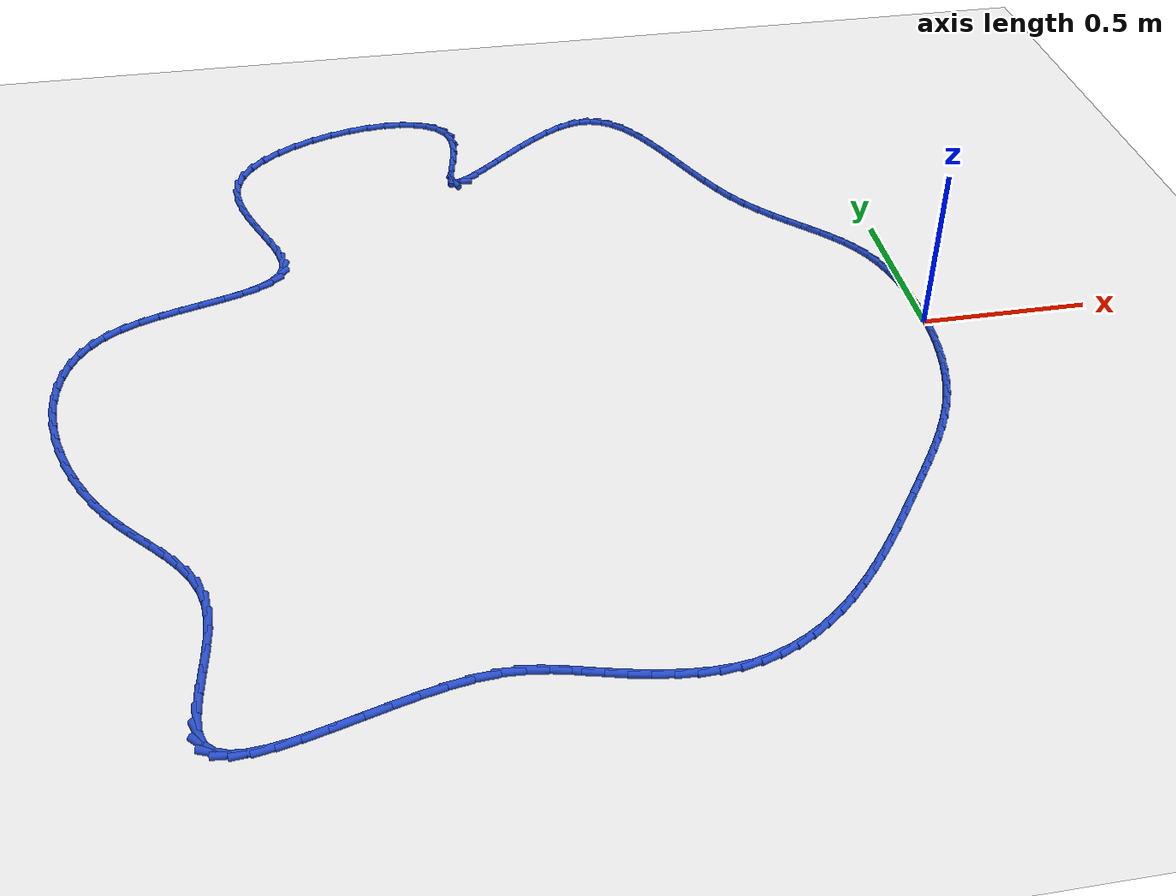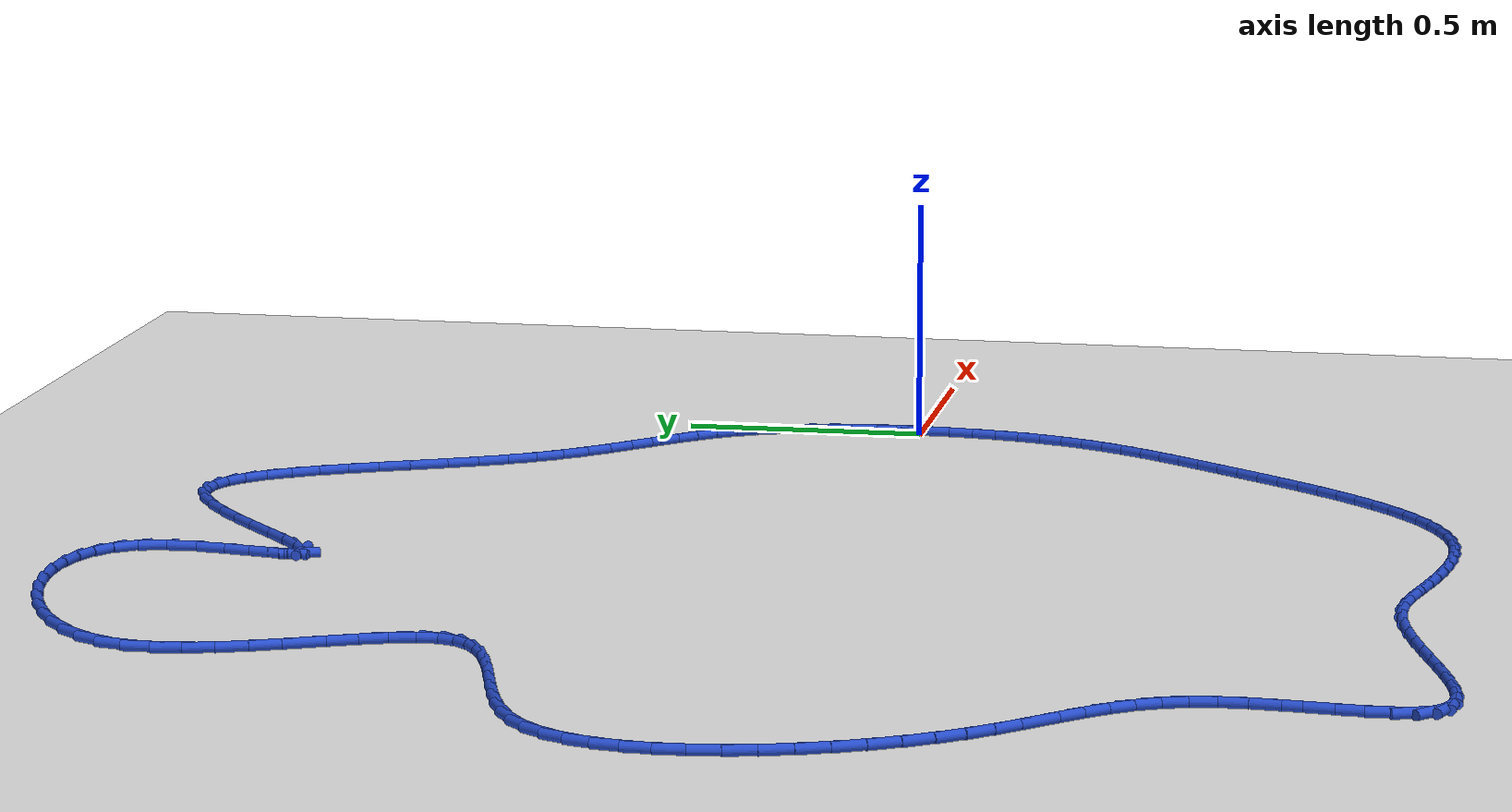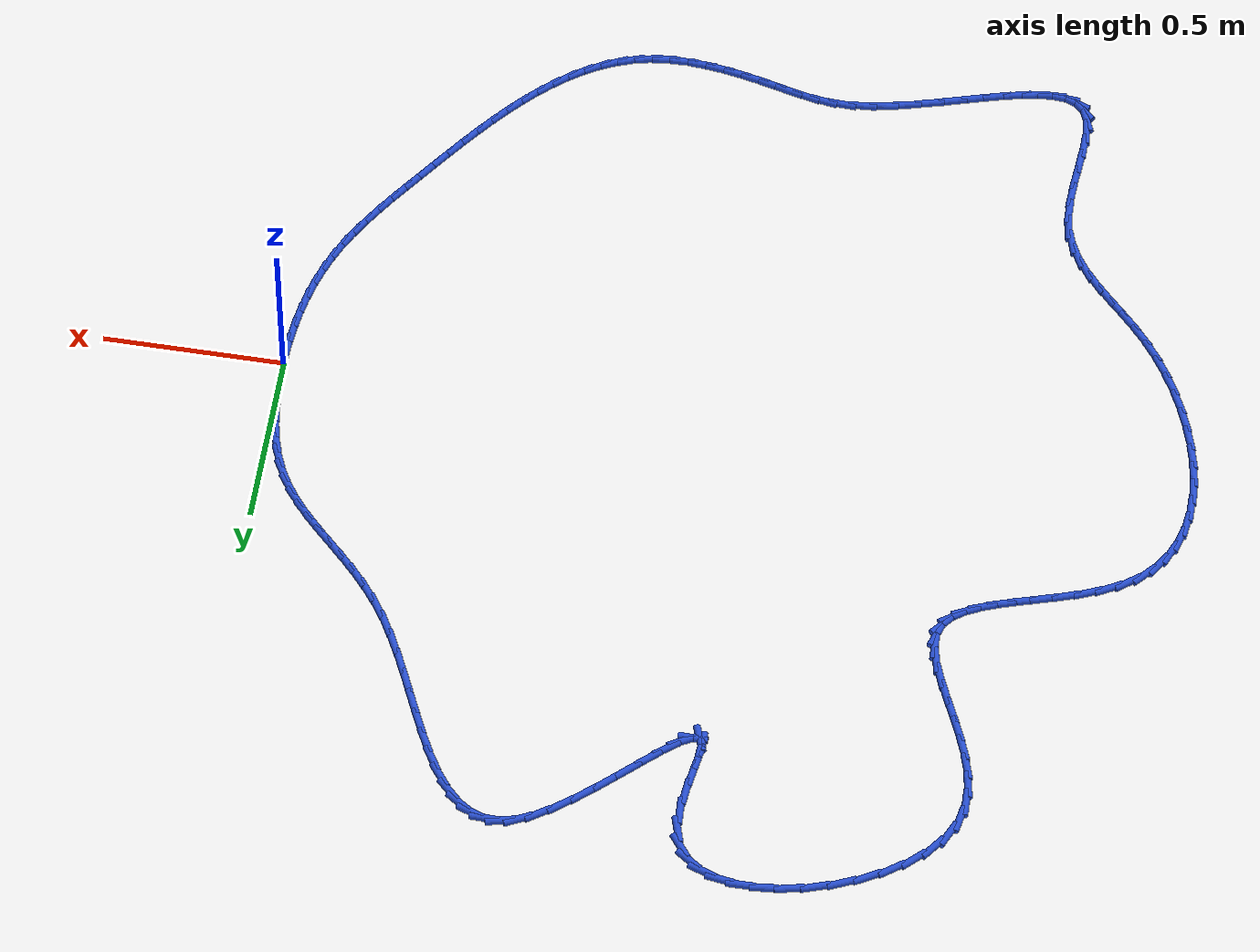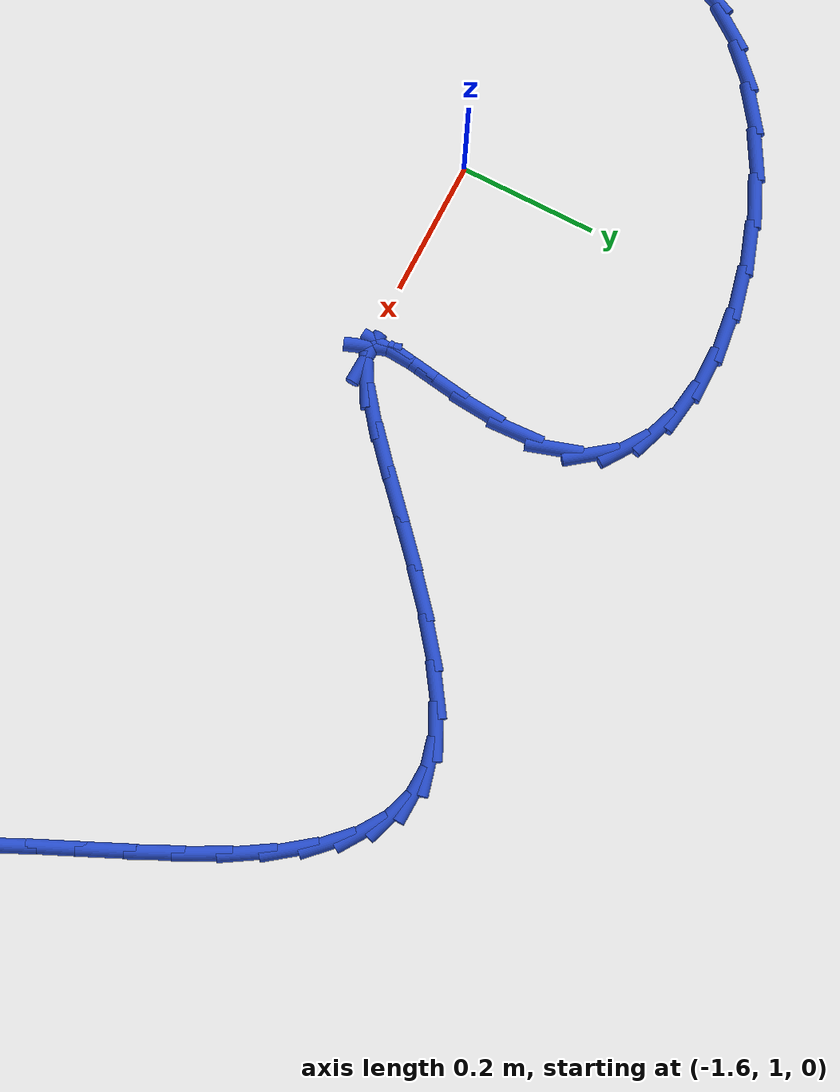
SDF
<sdf version="1.6">
 <world name="default">
  <light name="sun" type="directional">
   <pose>0 0 10 0 -0 0</pose>
   <diffuse>0.8 0.8 0.8 1</diffuse>
   <specular>0.2 0.2 0.2 1</specular>
   <attenuation>
    <range>1000</range>
    <constant>0.9</constant>
    <linear>0.01</linear>
    <quadratic>0.001</quadratic>
   </attenuation>
   <direction>-0.5 0.1 -0.9</direction>
  </light>
  <model name="ground_plane">
   <static>1</static>
   <link name="link">
    <collision name="collision">
     <geometry><plane><normal>0 0 1</normal><size>100 100</size></plane></geometry>
     <surface><friction><ode><mu>100</mu><mu2>50</mu2></ode></friction></surface>
    </collision>
    <visual name="visual">
     <cast_shadows>0</cast_shadows>
     <geometry><plane><normal>0 0 1</normal><size>100 100</size></plane></geometry>
     <material>
      <script><uri>file://media/materials/scripts/gazebo.material</uri><name>Gazebo/WhiteGlow</name></script>
     </material>
    </visual>
   </link>
  </model>
  <gravity>0 0 -9.8</gravity>
  <magnetic_field>6e-06 2.3e-05 -4.2e-05</magnetic_field>
  <atmosphere type="adiabatic"/>
  <physics name="default_physics" default="0" type="ode">
   <max_step_size>0.001</max_step_size>
   <real_time_factor>1</real_time_factor>
   <real_time_update_rate>1000</real_time_update_rate>
  </physics>
  <scene><ambient>0.4 0.4 0.4 1</ambient><background>0.7 0.7 0.7 1</background><shadows>1</shadows></scene>
  <spherical_coordinates>
   <surface_model>EARTH_WGS84</surface_model>
   <latitude_deg>0</latitude_deg>
   <longitude_deg>0</longitude_deg>
   <elevation>0</elevation>
   <heading_deg>0</heading_deg>
  </spherical_coordinates>
  <model name="line">
   <link name="link_0">
    <pose>4.336808689942018e-18 2.7755575615628914e-17 0.01 0 1.57 -1.5653542671570166</pose>
    <collision name="collision">
     <geometry><cylinder><radius>0.01</radius><length>0.08</length></cylinder></geometry>
    </collision>
    <visual name="visual">
     <material>
      <script><name>Gazebo/Blue</name><uri>file://media/materials/scripts/gazebo.material</uri></script>
     </material>
     <geometry><cylinder><radius>0.01</radius><length>0.08</length></cylinder></geometry>
    </visual>
   </link>
   <link name="link_1">
    <pose>-0.0002897953312062238 0.05325051352298232 0.01 0 1.57 -1.5207032406293453</pose>
    <collision name="collision">
     <geometry><cylinder><radius>0.01</radius><length>0.08</length></cylinder></geometry>
    </collision>
    <visual name="visual">
     <material>
      <script><name>Gazebo/Blue</name><uri>file://media/materials/scripts/gazebo.material</uri></script>
     </material>
     <geometry><cylinder><radius>0.01</radius><length>0.08</length></cylinder></geometry>
    </visual>
   </link>
   <link name="link_2">
    <pose>-0.0029570977130778395 0.10645288487942414 0.01 0 1.57 -1.4692730356951718</pose>
    <collision name="collision">
     <geometry><cylinder><radius>0.01</radius><length>0.08</length></cylinder></geometry>
    </collision>
    <visual name="visual">
     <material>
      <script><name>Gazebo/Blue</name><uri>file://media/materials/scripts/gazebo.material</uri></script>
     </material>
     <geometry><cylinder><radius>0.01</radius><length>0.08</length></cylinder></geometry>
    </visual>
   </link>
   <link name="link_3">
    <pose>-0.008315327640902419 0.15904976343120628 0.01 0 1.57 -1.4096182883418253</pose>
    <collision name="collision">
     <geometry><cylinder><radius>0.01</radius><length>0.08</length></cylinder></geometry>
    </collision>
    <visual name="visual">
     <material>
      <script><name>Gazebo/Blue</name><uri>file://media/materials/scripts/gazebo.material</uri></script>
     </material>
     <geometry><cylinder><radius>0.01</radius><length>0.08</length></cylinder></geometry>
    </visual>
   </link>
   <link name="link_4">
    <pose>-0.016677905609967535 0.21048379854020957 0.01 0 1.57 -1.3400302336169188</pose>
    <collision name="collision">
     <geometry><cylinder><radius>0.01</radius><length>0.08</length></cylinder></geometry>
    </collision>
    <visual name="visual">
     <material>
      <script><name>Gazebo/Blue</name><uri>file://media/materials/scripts/gazebo.material</uri></script>
     </material>
     <geometry><cylinder><radius>0.01</radius><length>0.08</length></cylinder></geometry>
    </visual>
   </link>
   <link name="link_5">
    <pose>-0.028358252115560756 0.260197639568315 0.01 0 1.57 -1.258572737377794</pose>
    <collision name="collision">
     <geometry><cylinder><radius>0.01</radius><length>0.08</length></cylinder></geometry>
    </collision>
    <visual name="visual">
     <material>
      <script><name>Gazebo/Blue</name><uri>file://media/materials/scripts/gazebo.material</uri></script>
     </material>
     <geometry><cylinder><radius>0.01</radius><length>0.08</length></cylinder></geometry>
    </visual>
   </link>
   <link name="link_6">
    <pose>-0.04366978765296965 0.30763393587740323 0.01 0 1.57 -1.1632319232325374</pose>
    <collision name="collision">
     <geometry><cylinder><radius>0.01</radius><length>0.08</length></cylinder></geometry>
    </collision>
    <visual name="visual">
     <material>
      <script><name>Gazebo/Blue</name><uri>file://media/materials/scripts/gazebo.material</uri></script>
     </material>
     <geometry><cylinder><radius>0.01</radius><length>0.08</length></cylinder></geometry>
    </visual>
   </link>
   <link name="link_7">
    <pose>-0.06292593271748181 0.35223533682935526 0.01 0 1.57 -1.0548973332844092</pose>
    <collision name="collision">
     <geometry><cylinder><radius>0.01</radius><length>0.08</length></cylinder></geometry>
    </collision>
    <visual name="visual">
     <material>
      <script><name>Gazebo/Blue</name><uri>file://media/materials/scripts/gazebo.material</uri></script>
     </material>
     <geometry><cylinder><radius>0.01</radius><length>0.08</length></cylinder></geometry>
    </visual>
   </link>
   <link name="link_8">
    <pose>-0.08636130278305484 0.39355814828937796 0.01 0 1.57 -0.9545919397772193</pose>
    <collision name="collision">
     <geometry><cylinder><radius>0.01</radius><length>0.08</length></cylinder></geometry>
    </collision>
    <visual name="visual">
     <material>
      <script><name>Gazebo/Blue</name><uri>file://media/materials/scripts/gazebo.material</uri></script>
     </material>
     <geometry><cylinder><radius>0.01</radius><length>0.08</length></cylinder></geometry>
    </visual>
   </link>
   <link name="link_9">
    <pose>-0.11360660851069125 0.4320296575426955 0.01 0 1.57 -0.8755505476731728</pose>
    <collision name="collision">
     <geometry><cylinder><radius>0.01</radius><length>0.08</length></cylinder></geometry>
    </collision>
    <visual name="visual">
     <material>
      <script><name>Gazebo/Blue</name><uri>file://media/materials/scripts/gazebo.material</uri></script>
     </material>
     <geometry><cylinder><radius>0.01</radius><length>0.08</length></cylinder></geometry>
    </visual>
   </link>
   <link name="link_10">
    <pose>-0.14401324618040653 0.46847999290338954 0.01 0 1.57 -0.8197589949420334</pose>
    <collision name="collision">
     <geometry><cylinder><radius>0.01</radius><length>0.08</length></cylinder></geometry>
    </collision>
    <visual name="visual">
     <material>
      <script><name>Gazebo/Blue</name><uri>file://media/materials/scripts/gazebo.material</uri></script>
     </material>
     <geometry><cylinder><radius>0.01</radius><length>0.08</length></cylinder></geometry>
    </visual>
   </link>
   <link name="link_11">
    <pose>-0.17693109837261767 0.5037414658180444 0.01 0 1.57 -0.7872059344161995</pose>
    <collision name="collision">
     <geometry><cylinder><radius>0.01</radius><length>0.08</length></cylinder></geometry>
    </collision>
    <visual name="visual">
     <material>
      <script><name>Gazebo/Blue</name><uri>file://media/materials/scripts/gazebo.material</uri></script>
     </material>
     <geometry><cylinder><radius>0.01</radius><length>0.08</length></cylinder></geometry>
    </visual>
   </link>
   <link name="link_12">
    <pose>-0.21171004766774176 0.5386463877332446 0.01 0 1.57 -0.7768619913404697</pose>
    <collision name="collision">
     <geometry><cylinder><radius>0.01</radius><length>0.08</length></cylinder></geometry>
    </collision>
    <visual name="visual">
     <material>
      <script><name>Gazebo/Blue</name><uri>file://media/materials/scripts/gazebo.material</uri></script>
     </material>
     <geometry><cylinder><radius>0.01</radius><length>0.08</length></cylinder></geometry>
    </visual>
   </link>
   <link name="link_13">
    <pose>-0.24769997664619597 0.5740270700955749 0.01 0 1.57 -0.7872818841349546</pose>
    <collision name="collision">
     <geometry><cylinder><radius>0.01</radius><length>0.08</length></cylinder></geometry>
    </collision>
    <visual name="visual">
     <material>
      <script><name>Gazebo/Blue</name><uri>file://media/materials/scripts/gazebo.material</uri></script>
     </material>
     <geometry><cylinder><radius>0.01</radius><length>0.08</length></cylinder></geometry>
    </visual>
   </link>
   <link name="link_14">
    <pose>-0.284250767888397 0.6107158243516193 0.01 0 1.57 -0.8168339501692937</pose>
    <collision name="collision">
     <geometry><cylinder><radius>0.01</radius><length>0.08</length></cylinder></geometry>
    </collision>
    <visual name="visual">
     <material>
      <script><name>Gazebo/Blue</name><uri>file://media/materials/scripts/gazebo.material</uri></script>
     </material>
     <geometry><cylinder><radius>0.01</radius><length>0.08</length></cylinder></geometry>
    </visual>
   </link>
   <link name="link_15">
    <pose>-0.32071230397476214 0.649544961947963 0.01 0 1.57 -0.8636610407866314</pose>
    <collision name="collision">
     <geometry><cylinder><radius>0.01</radius><length>0.08</length></cylinder></geometry>
    </collision>
    <visual name="visual">
     <material>
      <script><name>Gazebo/Blue</name><uri>file://media/materials/scripts/gazebo.material</uri></script>
     </material>
     <geometry><cylinder><radius>0.01</radius><length>0.08</length></cylinder></geometry>
    </visual>
   </link>
   <link name="link_16">
    <pose>-0.3564344674857085 0.6913467943311901 0.01 0 1.57 -0.9255077887292744</pose>
    <collision name="collision">
     <geometry><cylinder><radius>0.01</radius><length>0.08</length></cylinder></geometry>
    </collision>
    <visual name="visual">
     <material>
      <script><name>Gazebo/Blue</name><uri>file://media/materials/scripts/gazebo.material</uri></script>
     </material>
     <geometry><cylinder><radius>0.01</radius><length>0.08</length></cylinder></geometry>
    </visual>
   </link>
   <link name="link_17">
    <pose>-0.390767141001653 0.7369536329478852 0.01 0 1.57 -0.9984508834954018</pose>
    <collision name="collision">
     <geometry><cylinder><radius>0.01</radius><length>0.08</length></cylinder></geometry>
    </collision>
    <visual name="visual">
     <material>
      <script><name>Gazebo/Blue</name><uri>file://media/materials/scripts/gazebo.material</uri></script>
     </material>
     <geometry><cylinder><radius>0.01</radius><length>0.08</length></cylinder></geometry>
    </visual>
   </link>
   <link name="link_18">
    <pose>-0.42309504200383613 0.787130219534275 0.01 0 1.57 -1.0625769968892853</pose>
    <collision name="collision">
     <geometry><cylinder><radius>0.01</radius><length>0.08</length></cylinder></geometry>
    </collision>
    <visual name="visual">
     <material>
      <script><name>Gazebo/Blue</name><uri>file://media/materials/scripts/gazebo.material</uri></script>
     </material>
     <geometry><cylinder><radius>0.01</radius><length>0.08</length></cylinder></geometry>
    </visual>
   </link>
   <link name="link_19">
    <pose>-0.45338598497012783 0.8415102549956597 0.01 0 1.57 -1.106252419258811</pose>
    <collision name="collision">
     <geometry><cylinder><radius>0.01</radius><length>0.08</length></cylinder></geometry>
    </collision>
    <visual name="visual">
     <material>
      <script><name>Gazebo/Blue</name><uri>file://media/materials/scripts/gazebo.material</uri></script>
     </material>
     <geometry><cylinder><radius>0.01</radius><length>0.08</length></cylinder></geometry>
    </visual>
   </link>
   <link name="link_20">
    <pose>-0.4820905595473291 0.8987909949608659 0.01 0 1.57 -1.1324990940029072</pose>
    <collision name="collision">
     <geometry><cylinder><radius>0.01</radius><length>0.08</length></cylinder></geometry>
    </collision>
    <visual name="visual">
     <material>
      <script><name>Gazebo/Blue</name><uri>file://media/materials/scripts/gazebo.material</uri></script>
     </material>
     <geometry><cylinder><radius>0.01</radius><length>0.08</length></cylinder></geometry>
    </visual>
   </link>
   <link name="link_21">
    <pose>-0.5096739014452455 0.9576414798710554 0.01 0 1.57 -1.143208694709158</pose>
    <collision name="collision">
     <geometry><cylinder><radius>0.01</radius><length>0.08</length></cylinder></geometry>
    </collision>
    <visual name="visual">
     <material>
      <script><name>Gazebo/Blue</name><uri>file://media/materials/scripts/gazebo.material</uri></script>
     </material>
     <geometry><cylinder><radius>0.01</radius><length>0.08</length></cylinder></geometry>
    </visual>
   </link>
   <link name="link_22">
    <pose>-0.536601146373682 1.0167307501673892 0.01 0 1.57 -1.1388379147734444</pose>
    <collision name="collision">
     <geometry><cylinder><radius>0.01</radius><length>0.08</length></cylinder></geometry>
    </collision>
    <visual name="visual">
     <material>
      <script><name>Gazebo/Blue</name><uri>file://media/materials/scripts/gazebo.material</uri></script>
     </material>
     <geometry><cylinder><radius>0.01</radius><length>0.08</length></cylinder></geometry>
    </visual>
   </link>
   <link name="link_23">
    <pose>-0.5633374300424445 1.0747278462910297 0.01 0 1.57 -1.1183893006067103</pose>
    <collision name="collision">
     <geometry><cylinder><radius>0.01</radius><length>0.08</length></cylinder></geometry>
    </collision>
    <visual name="visual">
     <material>
      <script><name>Gazebo/Blue</name><uri>file://media/materials/scripts/gazebo.material</uri></script>
     </material>
     <geometry><cylinder><radius>0.01</radius><length>0.08</length></cylinder></geometry>
    </visual>
   </link>
   <link name="link_24">
    <pose>-0.590347888161338 1.1303018086831382 0.01 0 1.57 -1.0791502421996422</pose>
    <collision name="collision">
     <geometry><cylinder><radius>0.01</radius><length>0.08</length></cylinder></geometry>
    </collision>
    <visual name="visual">
     <material>
      <script><name>Gazebo/Blue</name><uri>file://media/materials/scripts/gazebo.material</uri></script>
     </material>
     <geometry><cylinder><radius>0.01</radius><length>0.08</length></cylinder></geometry>
    </visual>
   </link>
   <link name="link_25">
    <pose>-0.618097656440168 1.1821216777848758 0.01 0 1.57 -1.0161309922070074</pose>
    <collision name="collision">
     <geometry><cylinder><radius>0.01</radius><length>0.08</length></cylinder></geometry>
    </collision>
    <visual name="visual">
     <material>
      <script><name>Gazebo/Blue</name><uri>file://media/materials/scripts/gazebo.material</uri></script>
     </material>
     <geometry><cylinder><radius>0.01</radius><length>0.08</length></cylinder></geometry>
    </visual>
   </link>
   <link name="link_26">
    <pose>-0.6470518705887399 1.2288564940374045 0.01 0 1.57 -0.9212167148267709</pose>
    <collision name="collision">
     <geometry><cylinder><radius>0.01</radius><length>0.08</length></cylinder></geometry>
    </collision>
    <visual name="visual">
     <material>
      <script><name>Gazebo/Blue</name><uri>file://media/materials/scripts/gazebo.material</uri></script>
     </material>
     <geometry><cylinder><radius>0.01</radius><length>0.08</length></cylinder></geometry>
    </visual>
   </link>
   <link name="link_27">
    <pose>-0.6776756663168588 1.2691752978818853 0.01 0 1.57 -0.7825406760831308</pose>
    <collision name="collision">
     <geometry><cylinder><radius>0.01</radius><length>0.08</length></cylinder></geometry>
    </collision>
    <visual name="visual">
     <material>
      <script><name>Gazebo/Blue</name><uri>file://media/materials/scripts/gazebo.material</uri></script>
     </material>
     <geometry><cylinder><radius>0.01</radius><length>0.08</length></cylinder></geometry>
    </visual>
   </link>
   <link name="link_28">
    <pose>-0.7104341793343305 1.3017471297594807 0.01 0 1.57 -0.5864670858300862</pose>
    <collision name="collision">
     <geometry><cylinder><radius>0.01</radius><length>0.08</length></cylinder></geometry>
    </collision>
    <visual name="visual">
     <material>
      <script><name>Gazebo/Blue</name><uri>file://media/materials/scripts/gazebo.material</uri></script>
     </material>
     <geometry><cylinder><radius>0.01</radius><length>0.08</length></cylinder></geometry>
    </visual>
   </link>
   <link name="link_29">
    <pose>-0.74579254535096 1.325241030111352 0.01 0 1.57 -0.3282299355028631</pose>
    <collision name="collision">
     <geometry><cylinder><radius>0.01</radius><length>0.08</length></cylinder></geometry>
    </collision>
    <visual name="visual">
     <material>
      <script><name>Gazebo/Blue</name><uri>file://media/materials/scripts/gazebo.material</uri></script>
     </material>
     <geometry><cylinder><radius>0.01</radius><length>0.08</length></cylinder></geometry>
    </visual>
   </link>
   <link name="link_30">
    <pose>-0.7842159000765527 1.3383260393786602 0.01 0 1.57 -0.032052120000812</pose>
    <collision name="collision">
     <geometry><cylinder><radius>0.01</radius><length>0.08</length></cylinder></geometry>
    </collision>
    <visual name="visual">
     <material>
      <script><name>Gazebo/Blue</name><uri>file://media/materials/scripts/gazebo.material</uri></script>
     </material>
     <geometry><cylinder><radius>0.01</radius><length>0.08</length></cylinder></geometry>
    </visual>
   </link>
   <link name="link_31">
    <pose>-0.8261693792209142 1.339671198002567 0.01 0 1.57 0.24980036048068519</pose>
    <collision name="collision">
     <geometry><cylinder><radius>0.01</radius><length>0.08</length></cylinder></geometry>
    </collision>
    <visual name="visual">
     <material>
      <script><name>Gazebo/Blue</name><uri>file://media/materials/scripts/gazebo.material</uri></script>
     </material>
     <geometry><cylinder><radius>0.01</radius><length>0.08</length></cylinder></geometry>
    </visual>
   </link>
   <link name="link_32">
    <pose>-0.8721167716954523 1.3279486730198993 0.01 0 1.57 0.46335138029110495</pose>
    <collision name="collision">
     <geometry><cylinder><radius>0.01</radius><length>0.08</length></cylinder></geometry>
    </collision>
    <visual name="visual">
     <material>
      <script><name>Gazebo/Blue</name><uri>file://media/materials/scripts/gazebo.material</uri></script>
     </material>
     <geometry><cylinder><radius>0.01</radius><length>0.08</length></cylinder></geometry>
    </visual>
   </link>
   <link name="link_33">
    <pose>-0.9220091215972849 1.303020969766644 0.01 0 1.57 0.591791468082233</pose>
    <collision name="collision">
     <geometry><cylinder><radius>0.01</radius><length>0.08</length></cylinder></geometry>
    </collision>
    <visual name="visual">
     <material>
      <script><name>Gazebo/Blue</name><uri>file://media/materials/scripts/gazebo.material</uri></script>
     </material>
     <geometry><cylinder><radius>0.01</radius><length>0.08</length></cylinder></geometry>
    </visual>
   </link>
   <link name="link_34">
    <pose>-0.9745143272222495 1.267729419591458 0.01 0 1.57 0.6688519637819874</pose>
    <collision name="collision">
     <geometry><cylinder><radius>0.01</radius><length>0.08</length></cylinder></geometry>
    </collision>
    <visual name="visual">
     <material>
      <script><name>Gazebo/Blue</name><uri>file://media/materials/scripts/gazebo.material</uri></script>
     </material>
     <geometry><cylinder><radius>0.01</radius><length>0.08</length></cylinder></geometry>
    </visual>
   </link>
   <link name="link_35">
    <pose>-1.0281028301722723 1.2253737500249526 0.01 0 1.57 0.7147721482131322</pose>
    <collision name="collision">
     <geometry><cylinder><radius>0.01</radius><length>0.08</length></cylinder></geometry>
    </collision>
    <visual name="visual">
     <material>
      <script><name>Gazebo/Blue</name><uri>file://media/materials/scripts/gazebo.material</uri></script>
     </material>
     <geometry><cylinder><radius>0.01</radius><length>0.08</length></cylinder></geometry>
    </visual>
   </link>
   <link name="link_36">
    <pose>-1.0812450720492814 1.1792536885977387 0.01 0 1.57 0.7385614153455848</pose>
    <collision name="collision">
     <geometry><cylinder><radius>0.01</radius><length>0.08</length></cylinder></geometry>
    </collision>
    <visual name="visual">
     <material>
      <script><name>Gazebo/Blue</name><uri>file://media/materials/scripts/gazebo.material</uri></script>
     </material>
     <geometry><cylinder><radius>0.01</radius><length>0.08</length></cylinder></geometry>
    </visual>
   </link>
   <link name="link_37">
    <pose>-1.132411494455203 1.1326689628404278 0.01 0 1.57 0.7426351480196461</pose>
    <collision name="collision">
     <geometry><cylinder><radius>0.01</radius><length>0.08</length></cylinder></geometry>
    </collision>
    <visual name="visual">
     <material>
      <script><name>Gazebo/Blue</name><uri>file://media/materials/scripts/gazebo.material</uri></script>
     </material>
     <geometry><cylinder><radius>0.01</radius><length>0.08</length></cylinder></geometry>
    </visual>
   </link>
   <link name="link_38">
    <pose>-1.1800725389919642 1.0889193002836308 0.01 0 1.57 0.7230268346368294</pose>
    <collision name="collision">
     <geometry><cylinder><radius>0.01</radius><length>0.08</length></cylinder></geometry>
    </collision>
    <visual name="visual">
     <material>
      <script><name>Gazebo/Blue</name><uri>file://media/materials/scripts/gazebo.material</uri></script>
     </material>
     <geometry><cylinder><radius>0.01</radius><length>0.08</length></cylinder></geometry>
    </visual>
   </link>
   <link name="link_39">
    <pose>-1.2226986472614922 1.0513044284579591 0.01 0 1.57 0.663327273774626</pose>
    <collision name="collision">
     <geometry><cylinder><radius>0.01</radius><length>0.08</length></cylinder></geometry>
    </collision>
    <visual name="visual">
     <material>
      <script><name>Gazebo/Blue</name><uri>file://media/materials/scripts/gazebo.material</uri></script>
     </material>
     <geometry><cylinder><radius>0.01</radius><length>0.08</length></cylinder></geometry>
    </visual>
   </link>
   <link name="link_40">
    <pose>-1.2587602608657138 1.0231240748940236 0.01 0 1.57 0.5045970312165727</pose>
    <collision name="collision">
     <geometry><cylinder><radius>0.01</radius><length>0.08</length></cylinder></geometry>
    </collision>
    <visual name="visual">
     <material>
      <script><name>Gazebo/Blue</name><uri>file://media/materials/scripts/gazebo.material</uri></script>
     </material>
     <geometry><cylinder><radius>0.01</radius><length>0.08</length></cylinder></geometry>
    </visual>
   </link>
   <link name="link_41">
    <pose>-1.286727821406556 1.0076779671224356 0.01 0 1.57 -0.03203587334514121</pose>
    <collision name="collision">
     <geometry><cylinder><radius>0.01</radius><length>0.08</length></cylinder></geometry>
    </collision>
    <visual name="visual">
     <material>
      <script><name>Gazebo/Blue</name><uri>file://media/materials/scripts/gazebo.material</uri></script>
     </material>
     <geometry><cylinder><radius>0.01</radius><length>0.08</length></cylinder></geometry>
    </visual>
   </link>
   <link name="link_42">
    <pose>-1.305071770485946 1.0082658326738065 0.01 0 1.57 -1.217949614169399</pose>
    <collision name="collision">
     <geometry><cylinder><radius>0.01</radius><length>0.08</length></cylinder></geometry>
    </collision>
    <visual name="visual">
     <material>
      <script><name>Gazebo/Blue</name><uri>file://media/materials/scripts/gazebo.material</uri></script>
     </material>
     <geometry><cylinder><radius>0.01</radius><length>0.08</length></cylinder></geometry>
    </visual>
   </link>
   <link name="link_43">
    <pose>-1.3123570567298515 1.0280489426942956 0.01 0 1.57 1.5056751465555551</pose>
    <collision name="collision">
     <geometry><cylinder><radius>0.01</radius><length>0.08</length></cylinder></geometry>
    </collision>
    <visual name="visual">
     <material>
      <script><name>Gazebo/Blue</name><uri>file://media/materials/scripts/gazebo.material</uri></script>
     </material>
     <geometry><cylinder><radius>0.01</radius><length>0.08</length></cylinder></geometry>
    </visual>
   </link>
   <link name="link_44">
    <pose>-1.3098688821073046 1.066203293727551 0.01 0 1.57 1.4175036555119238</pose>
    <collision name="collision">
     <geometry><cylinder><radius>0.01</radius><length>0.08</length></cylinder></geometry>
    </collision>
    <visual name="visual">
     <material>
      <script><name>Gazebo/Blue</name><uri>file://media/materials/scripts/gazebo.material</uri></script>
     </material>
     <geometry><cylinder><radius>0.01</radius><length>0.08</length></cylinder></geometry>
    </visual>
   </link>
   <link name="link_45">
    <pose>-1.3019562214100033 1.117416338612578 0.01 0 1.57 1.4216280620579</pose>
    <collision name="collision">
     <geometry><cylinder><radius>0.01</radius><length>0.08</length></cylinder></geometry>
    </collision>
    <visual name="visual">
     <material>
      <script><name>Gazebo/Blue</name><uri>file://media/materials/scripts/gazebo.material</uri></script>
     </material>
     <geometry><cylinder><radius>0.01</radius><length>0.08</length></cylinder></geometry>
    </visual>
   </link>
   <link name="link_46">
    <pose>-1.2931315650826976 1.1761359735379382 0.01 0 1.57 1.484906186558458</pose>
    <collision name="collision">
     <geometry><cylinder><radius>0.01</radius><length>0.08</length></cylinder></geometry>
    </collision>
    <visual name="visual">
     <material>
      <script><name>Gazebo/Blue</name><uri>file://media/materials/scripts/gazebo.material</uri></script>
     </material>
     <geometry><cylinder><radius>0.01</radius><length>0.08</length></cylinder></geometry>
    </visual>
   </link>
   <link name="link_47">
    <pose>-1.2879074035701361 1.2368100946921947 0.01 0 1.57 -1.520226292028374</pose>
    <collision name="collision">
     <geometry><cylinder><radius>0.01</radius><length>0.08</length></cylinder></geometry>
    </collision>
    <visual name="visual">
     <material>
      <script><name>Gazebo/Blue</name><uri>file://media/materials/scripts/gazebo.material</uri></script>
     </material>
     <geometry><cylinder><radius>0.01</radius><length>0.08</length></cylinder></geometry>
    </visual>
   </link>
   <link name="link_48">
    <pose>-1.2907962273170686 1.293886598263909 0.01 0 1.57 -1.263776333785228</pose>
    <collision name="collision">
     <geometry><cylinder><radius>0.01</radius><length>0.08</length></cylinder></geometry>
    </collision>
    <visual name="visual">
     <material>
      <script><name>Gazebo/Blue</name><uri>file://media/materials/scripts/gazebo.material</uri></script>
     </material>
     <geometry><cylinder><radius>0.01</radius><length>0.08</length></cylinder></geometry>
    </visual>
   </link>
   <link name="link_49">
    <pose>-1.3060652395106764 1.3420470161652145 0.01 0 1.57 -0.9198314015674852</pose>
    <collision name="collision">
     <geometry><cylinder><radius>0.01</radius><length>0.08</length></cylinder></geometry>
    </collision>
    <visual name="visual">
     <material>
      <script><name>Gazebo/Blue</name><uri>file://media/materials/scripts/gazebo.material</uri></script>
     </material>
     <geometry><cylinder><radius>0.01</radius><length>0.08</length></cylinder></geometry>
    </visual>
   </link>
   <link name="link_50">
    <pose>-1.3344615258667254 1.379325786613444 0.01 0 1.57 -0.5969900036822664</pose>
    <collision name="collision">
     <geometry><cylinder><radius>0.01</radius><length>0.08</length></cylinder></geometry>
    </collision>
    <visual name="visual">
     <material>
      <script><name>Gazebo/Blue</name><uri>file://media/materials/scripts/gazebo.material</uri></script>
     </material>
     <geometry><cylinder><radius>0.01</radius><length>0.08</length></cylinder></geometry>
    </visual>
   </link>
   <link name="link_51">
    <pose>-1.3740971554364683 1.4062671970171843 0.01 0 1.57 -0.3382347308395008</pose>
    <collision name="collision">
     <geometry><cylinder><radius>0.01</radius><length>0.08</length></cylinder></geometry>
    </collision>
    <visual name="visual">
     <material>
      <script><name>Gazebo/Blue</name><uri>file://media/materials/scripts/gazebo.material</uri></script>
     </material>
     <geometry><cylinder><radius>0.01</radius><length>0.08</length></cylinder></geometry>
    </visual>
   </link>
   <link name="link_52">
    <pose>-1.4230205974114285 1.4234761135504843 0.01 0 1.57 -0.14266664585292355</pose>
    <collision name="collision">
     <geometry><cylinder><radius>0.01</radius><length>0.08</length></cylinder></geometry>
    </collision>
    <visual name="visual">
     <material>
      <script><name>Gazebo/Blue</name><uri>file://media/materials/scripts/gazebo.material</uri></script>
     </material>
     <geometry><cylinder><radius>0.01</radius><length>0.08</length></cylinder></geometry>
    </visual>
   </link>
   <link name="link_53">
    <pose>-1.4792803209831296 1.431557402387393 0.01 0 1.57 0.0071614713690252175</pose>
    <collision name="collision">
     <geometry><cylinder><radius>0.01</radius><length>0.08</length></cylinder></geometry>
    </collision>
    <visual name="visual">
     <material>
      <script><name>Gazebo/Blue</name><uri>file://media/materials/scripts/gazebo.material</uri></script>
     </material>
     <geometry><cylinder><radius>0.01</radius><length>0.08</length></cylinder></geometry>
    </visual>
   </link>
   <link name="link_54">
    <pose>-1.540924795343094 1.431115929701958 0.01 0 1.57 0.12775255188260023</pose>
    <collision name="collision">
     <geometry><cylinder><radius>0.01</radius><length>0.08</length></cylinder></geometry>
    </collision>
    <visual name="visual">
     <material>
      <script><name>Gazebo/Blue</name><uri>file://media/materials/scripts/gazebo.material</uri></script>
     </material>
     <geometry><cylinder><radius>0.01</radius><length>0.08</length></cylinder></geometry>
    </visual>
   </link>
   <link name="link_55">
    <pose>-1.6060024896828478 1.4227565616682294 0.01 0 1.57 0.23125246474559782</pose>
    <collision name="collision">
     <geometry><cylinder><radius>0.01</radius><length>0.08</length></cylinder></geometry>
    </collision>
    <visual name="visual">
     <material>
      <script><name>Gazebo/Blue</name><uri>file://media/materials/scripts/gazebo.material</uri></script>
     </material>
     <geometry><cylinder><radius>0.01</radius><length>0.08</length></cylinder></geometry>
    </visual>
   </link>
   <link name="link_56">
    <pose>-1.6725618731939114 1.4070841644602556 0.01 0 1.57 0.3265188963801273</pose>
    <collision name="collision">
     <geometry><cylinder><radius>0.01</radius><length>0.08</length></cylinder></geometry>
    </collision>
    <visual name="visual">
     <material>
      <script><name>Gazebo/Blue</name><uri>file://media/materials/scripts/gazebo.material</uri></script>
     </material>
     <geometry><cylinder><radius>0.01</radius><length>0.08</length></cylinder></geometry>
    </visual>
   </link>
   <link name="link_57">
    <pose>-1.7386514150678092 1.3847036042520844 0.01 0 1.57 0.42067288449298074</pose>
    <collision name="collision">
     <geometry><cylinder><radius>0.01</radius><length>0.08</length></cylinder></geometry>
    </collision>
    <visual name="visual">
     <material>
      <script><name>Gazebo/Blue</name><uri>file://media/materials/scripts/gazebo.material</uri></script>
     </material>
     <geometry><cylinder><radius>0.01</radius><length>0.08</length></cylinder></geometry>
    </visual>
   </link>
   <link name="link_58">
    <pose>-1.8023195844960653 1.356219747217765 0.01 0 1.57 0.5204073733523381</pose>
    <collision name="collision">
     <geometry><cylinder><radius>0.01</radius><length>0.08</length></cylinder></geometry>
    </collision>
    <visual name="visual">
     <material>
      <script><name>Gazebo/Blue</name><uri>file://media/materials/scripts/gazebo.material</uri></script>
     </material>
     <geometry><cylinder><radius>0.01</radius><length>0.08</length></cylinder></geometry>
    </visual>
   </link>
   <link name="link_59">
    <pose>-1.8616148506702022 1.3222374595313464 0.01 0 1.57 0.6331240848782561</pose>
    <collision name="collision">
     <geometry><cylinder><radius>0.01</radius><length>0.08</length></cylinder></geometry>
    </collision>
    <visual name="visual">
     <material>
      <script><name>Gazebo/Blue</name><uri>file://media/materials/scripts/gazebo.material</uri></script>
     </material>
     <geometry><cylinder><radius>0.01</radius><length>0.08</length></cylinder></geometry>
    </visual>
   </link>
   <link name="link_60">
    <pose>-1.9145856827817438 1.283361607366877 0.01 0 1.57 0.7679821357870458</pose>
    <collision name="collision">
     <geometry><cylinder><radius>0.01</radius><length>0.08</length></cylinder></geometry>
    </collision>
    <visual name="visual">
     <material>
      <script><name>Gazebo/Blue</name><uri>file://media/materials/scripts/gazebo.material</uri></script>
     </material>
     <geometry><cylinder><radius>0.01</radius><length>0.08</length></cylinder></geometry>
    </visual>
   </link>
   <link name="link_61">
    <pose>-1.9592805500222141 1.2401970568984049 0.01 0 1.57 0.9364961331188776</pose>
    <collision name="collision">
     <geometry><cylinder><radius>0.01</radius><length>0.08</length></cylinder></geometry>
    </collision>
    <visual name="visual">
     <material>
      <script><name>Gazebo/Blue</name><uri>file://media/materials/scripts/gazebo.material</uri></script>
     </material>
     <geometry><cylinder><radius>0.01</radius><length>0.08</length></cylinder></geometry>
    </visual>
   </link>
   <link name="link_62">
    <pose>-1.9937479215831346 1.1933486742999793 0.01 0 1.57 1.1508773828364496</pose>
    <collision name="collision">
     <geometry><cylinder><radius>0.01</radius><length>0.08</length></cylinder></geometry>
    </collision>
    <visual name="visual">
     <material>
      <script><name>Gazebo/Blue</name><uri>file://media/materials/scripts/gazebo.material</uri></script>
     </material>
     <geometry><cylinder><radius>0.01</radius><length>0.08</length></cylinder></geometry>
    </visual>
   </link>
   <link name="link_63">
    <pose>-2.0160392220537315 1.1434213904772648 0.01 0 1.57 1.3958968213287948</pose>
    <collision name="collision">
     <geometry><cylinder><radius>0.01</radius><length>0.08</length></cylinder></geometry>
    </collision>
    <visual name="visual">
     <material>
      <script><name>Gazebo/Blue</name><uri>file://media/materials/scripts/gazebo.material</uri></script>
     </material>
     <geometry><cylinder><radius>0.01</radius><length>0.08</length></cylinder></geometry>
    </visual>
   </link>
   <link name="link_64">
    <pose>-2.0252945711457717 1.0910439818557995 0.01 0 1.57 -1.5351315133772294</pose>
    <collision name="collision">
     <geometry><cylinder><radius>0.01</radius><length>0.08</length></cylinder></geometry>
    </collision>
    <visual name="visual">
     <material>
      <script><name>Gazebo/Blue</name><uri>file://media/materials/scripts/gazebo.material</uri></script>
     </material>
     <geometry><cylinder><radius>0.01</radius><length>0.08</length></cylinder></geometry>
    </visual>
   </link>
   <link name="link_65">
    <pose>-2.0233628794983916 1.0369045550873264 0.01 0 1.57 -1.3766292983681143</pose>
    <collision name="collision">
     <geometry><cylinder><radius>0.01</radius><length>0.08</length></cylinder></geometry>
    </collision>
    <visual name="visual">
     <material>
      <script><name>Gazebo/Blue</name><uri>file://media/materials/scripts/gazebo.material</uri></script>
     </material>
     <geometry><cylinder><radius>0.01</radius><length>0.08</length></cylinder></geometry>
    </visual>
   </link>
   <link name="link_66">
    <pose>-2.0125072651991713 0.9817002891448833 0.01 0 1.57 -1.2654511479101467</pose>
    <collision name="collision">
     <geometry><cylinder><radius>0.01</radius><length>0.08</length></cylinder></geometry>
    </collision>
    <visual name="visual">
     <material>
      <script><name>Gazebo/Blue</name><uri>file://media/materials/scripts/gazebo.material</uri></script>
     </material>
     <geometry><cylinder><radius>0.01</radius><length>0.08</length></cylinder></geometry>
    </visual>
   </link>
   <link name="link_67">
    <pose>-1.9949908463356891 0.9261283630015092 0.01 0 1.57 -1.1931467327325218</pose>
    <collision name="collision">
     <geometry><cylinder><radius>0.01</radius><length>0.08</length></cylinder></geometry>
    </collision>
    <visual name="visual">
     <material>
      <script><name>Gazebo/Blue</name><uri>file://media/materials/scripts/gazebo.material</uri></script>
     </material>
     <geometry><cylinder><radius>0.01</radius><length>0.08</length></cylinder></geometry>
    </visual>
   </link>
   <link name="link_68">
    <pose>-1.973076740995524 0.8708859556302413 0.01 0 1.57 -1.1532991819926677</pose>
    <collision name="collision">
     <geometry><cylinder><radius>0.01</radius><length>0.08</length></cylinder></geometry>
    </collision>
    <visual name="visual">
     <material>
      <script><name>Gazebo/Blue</name><uri>file://media/materials/scripts/gazebo.material</uri></script>
     </material>
     <geometry><cylinder><radius>0.01</radius><length>0.08</length></cylinder></geometry>
    </visual>
   </link>
   <link name="link_69">
    <pose>-1.9490280672662557 0.8166702460041186 0.01 0 1.57 -1.1432187772029583</pose>
    <collision name="collision">
     <geometry><cylinder><radius>0.01</radius><length>0.08</length></cylinder></geometry>
    </collision>
    <visual name="visual">
     <material>
      <script><name>Gazebo/Blue</name><uri>file://media/materials/scripts/gazebo.material</uri></script>
     </material>
     <geometry><cylinder><radius>0.01</radius><length>0.08</length></cylinder></geometry>
    </visual>
   </link>
   <link name="link_70">
    <pose>-1.9251079432354623 0.7641784130961786 0.01 0 1.57 -1.164731607844907</pose>
    <collision name="collision">
     <geometry><cylinder><radius>0.01</radius><length>0.08</length></cylinder></geometry>
    </collision>
    <visual name="visual">
     <material>
      <script><name>Gazebo/Blue</name><uri>file://media/materials/scripts/gazebo.material</uri></script>
     </material>
     <geometry><cylinder><radius>0.01</radius><length>0.08</length></cylinder></geometry>
    </visual>
   </link>
   <link name="link_71">
    <pose>-1.903579486990723 0.7141076358794591 0.01 0 1.57 -1.2257922560021717</pose>
    <collision name="collision">
     <geometry><cylinder><radius>0.01</radius><length>0.08</length></cylinder></geometry>
    </collision>
    <visual name="visual">
     <material>
      <script><name>Gazebo/Blue</name><uri>file://media/materials/scripts/gazebo.material</uri></script>
     </material>
     <geometry><cylinder><radius>0.01</radius><length>0.08</length></cylinder></geometry>
    </visual>
   </link>
   <link name="link_72">
    <pose>-1.886705816619617 0.6671550933269992 0.01 0 1.57 -1.3439744929055737</pose>
    <collision name="collision">
     <geometry><cylinder><radius>0.01</radius><length>0.08</length></cylinder></geometry>
    </collision>
    <visual name="visual">
     <material>
      <script><name>Gazebo/Blue</name><uri>file://media/materials/scripts/gazebo.material</uri></script>
     </material>
     <geometry><cylinder><radius>0.01</radius><length>0.08</length></cylinder></geometry>
    </visual>
   </link>
   <link name="link_73">
    <pose>-1.876750050209723 0.624017964411836 0.01 0 1.57 -1.5507406689815804</pose>
    <collision name="collision">
     <geometry><cylinder><radius>0.01</radius><length>0.08</length></cylinder></geometry>
    </collision>
    <visual name="visual">
     <material>
      <script><name>Gazebo/Blue</name><uri>file://media/materials/scripts/gazebo.material</uri></script>
     </material>
     <geometry><cylinder><radius>0.01</radius><length>0.08</length></cylinder></geometry>
    </visual>
   </link>
   <link name="link_74">
    <pose>-1.8759753058486206 0.5853934281070077 0.01 0 1.57 1.2622620692266882</pose>
    <collision name="collision">
     <geometry><cylinder><radius>0.01</radius><length>0.08</length></cylinder></geometry>
    </collision>
    <visual name="visual">
     <material>
      <script><name>Gazebo/Blue</name><uri>file://media/materials/scripts/gazebo.material</uri></script>
     </material>
     <geometry><cylinder><radius>0.01</radius><length>0.08</length></cylinder></geometry>
    </visual>
   </link>
   <link name="link_75">
    <pose>-1.886627299951994 0.5519714356031784 0.01 0 1.57 0.8878031181250129</pose>
    <collision name="collision">
     <geometry><cylinder><radius>0.01</radius><length>0.08</length></cylinder></geometry>
    </collision>
    <visual name="visual">
     <material>
      <script><name>Gazebo/Blue</name><uri>file://media/materials/scripts/gazebo.material</uri></script>
     </material>
     <geometry><cylinder><radius>0.01</radius><length>0.08</length></cylinder></geometry>
    </visual>
   </link>
   <link name="link_76">
    <pose>-1.909512378010174 0.5238440955464572 0.01 0 1.57 0.618217324122047</pose>
    <collision name="collision">
     <geometry><cylinder><radius>0.01</radius><length>0.08</length></cylinder></geometry>
    </collision>
    <visual name="visual">
     <material>
      <script><name>Gazebo/Blue</name><uri>file://media/materials/scripts/gazebo.material</uri></script>
     </material>
     <geometry><cylinder><radius>0.01</radius><length>0.08</length></cylinder></geometry>
    </visual>
   </link>
   <link name="link_77">
    <pose>-1.9429428647434916 0.5000676253494684 0.01 0 1.57 0.4531796947097287</pose>
    <collision name="collision">
     <geometry><cylinder><radius>0.01</radius><length>0.08</length></cylinder></geometry>
    </collision>
    <visual name="visual">
     <material>
      <script><name>Gazebo/Blue</name><uri>file://media/materials/scripts/gazebo.material</uri></script>
     </material>
     <geometry><cylinder><radius>0.01</radius><length>0.08</length></cylinder></geometry>
    </visual>
   </link>
   <link name="link_78">
    <pose>-1.9849825608152734 0.47959501798699083 0.01 0 1.57 0.3578432331282109</pose>
    <collision name="collision">
     <geometry><cylinder><radius>0.01</radius><length>0.08</length></cylinder></geometry>
    </collision>
    <visual name="visual">
     <material>
      <script><name>Gazebo/Blue</name><uri>file://media/materials/scripts/gazebo.material</uri></script>
     </material>
     <geometry><cylinder><radius>0.01</radius><length>0.08</length></cylinder></geometry>
    </visual>
   </link>
   <link name="link_79">
    <pose>-2.0336952668888446 0.4613792664338011 0.01 0 1.57 0.30803984114194716</pose>
    <collision name="collision">
     <geometry><cylinder><radius>0.01</radius><length>0.08</length></cylinder></geometry>
    </collision>
    <visual name="visual">
     <material>
      <script><name>Gazebo/Blue</name><uri>file://media/materials/scripts/gazebo.material</uri></script>
     </material>
     <geometry><cylinder><radius>0.01</radius><length>0.08</length></cylinder></geometry>
    </visual>
   </link>
   <link name="link_80">
    <pose>-2.08714478362753 0.44437336366467745 0.01 0 1.57 0.29093516612739784</pose>
    <collision name="collision">
     <geometry><cylinder><radius>0.01</radius><length>0.08</length></cylinder></geometry>
    </collision>
    <visual name="visual">
     <material>
      <script><name>Gazebo/Blue</name><uri>file://media/materials/scripts/gazebo.material</uri></script>
     </material>
     <geometry><cylinder><radius>0.01</radius><length>0.08</length></cylinder></geometry>
    </visual>
   </link>
   <link name="link_81">
    <pose>-2.143394911694655 0.427530302654397 0.01 0 1.57 0.30095256134408305</pose>
    <collision name="collision">
     <geometry><cylinder><radius>0.01</radius><length>0.08</length></cylinder></geometry>
    </collision>
    <visual name="visual">
     <material>
      <script><name>Gazebo/Blue</name><uri>file://media/materials/scripts/gazebo.material</uri></script>
     </material>
     <geometry><cylinder><radius>0.01</radius><length>0.08</length></cylinder></geometry>
    </visual>
   </link>
   <link name="link_82">
    <pose>-2.2005094517535473 0.40980307637773744 0.01 0 1.57 0.33736510717951823</pose>
    <collision name="collision">
     <geometry><cylinder><radius>0.01</radius><length>0.08</length></cylinder></geometry>
    </collision>
    <visual name="visual">
     <material>
      <script><name>Gazebo/Blue</name><uri>file://media/materials/scripts/gazebo.material</uri></script>
     </material>
     <geometry><cylinder><radius>0.01</radius><length>0.08</length></cylinder></geometry>
    </visual>
   </link>
   <link name="link_83">
    <pose>-2.2565522044675297 0.3901446778094767 0.01 0 1.57 0.40341564405396885</pose>
    <collision name="collision">
     <geometry><cylinder><radius>0.01</radius><length>0.08</length></cylinder></geometry>
    </collision>
    <visual name="visual">
     <material>
      <script><name>Gazebo/Blue</name><uri>file://media/materials/scripts/gazebo.material</uri></script>
     </material>
     <geometry><cylinder><radius>0.01</radius><length>0.08</length></cylinder></geometry>
    </visual>
   </link>
   <link name="link_84">
    <pose>-2.309586970499929 0.3675080999243918 0.01 0 1.57 0.5062205662328486</pose>
    <collision name="collision">
     <geometry><cylinder><radius>0.01</radius><length>0.08</length></cylinder></geometry>
    </collision>
    <visual name="visual">
     <material>
      <script><name>Gazebo/Blue</name><uri>file://media/materials/scripts/gazebo.material</uri></script>
     </material>
     <geometry><cylinder><radius>0.01</radius><length>0.08</length></cylinder></geometry>
    </visual>
   </link>
   <link name="link_85">
    <pose>-2.3576775505140697 0.34084633569726086 0.01 0 1.57 0.6556380966834249</pose>
    <collision name="collision">
     <geometry><cylinder><radius>0.01</radius><length>0.08</length></cylinder></geometry>
    </collision>
    <visual name="visual">
     <material>
      <script><name>Gazebo/Blue</name><uri>file://media/materials/scripts/gazebo.material</uri></script>
     </material>
     <geometry><cylinder><radius>0.01</radius><length>0.08</length></cylinder></geometry>
    </visual>
   </link>
   <link name="link_86">
    <pose>-2.3989128618126854 0.30913064124748046 0.01 0 1.57 0.8372037314220584</pose>
    <collision name="collision">
     <geometry><cylinder><radius>0.01</radius><length>0.08</length></cylinder></geometry>
    </collision>
    <visual name="visual">
     <material>
      <script><name>Gazebo/Blue</name><uri>file://media/materials/scripts/gazebo.material</uri></script>
     </material>
     <geometry><cylinder><radius>0.01</radius><length>0.08</length></cylinder></geometry>
    </visual>
   </link>
   <link name="link_87">
    <pose>-2.4323500220021153 0.2720362833655599 0.01 0 1.57 1.0161559835718779</pose>
    <collision name="collision">
     <geometry><cylinder><radius>0.01</radius><length>0.08</length></cylinder></geometry>
    </collision>
    <visual name="visual">
     <material>
      <script><name>Gazebo/Blue</name><uri>file://media/materials/scripts/gazebo.material</uri></script>
     </material>
     <geometry><cylinder><radius>0.01</radius><length>0.08</length></cylinder></geometry>
    </visual>
   </link>
   <link name="link_88">
    <pose>-2.4582991465624806 0.2301496253070057 0.01 0 1.57 1.1820463625686763</pose>
    <collision name="collision">
     <geometry><cylinder><radius>0.01</radius><length>0.08</length></cylinder></geometry>
    </collision>
    <visual name="visual">
     <material>
      <script><name>Gazebo/Blue</name><uri>file://media/materials/scripts/gazebo.material</uri></script>
     </material>
     <geometry><cylinder><radius>0.01</radius><length>0.08</length></cylinder></geometry>
    </visual>
   </link>
   <link name="link_89">
    <pose>-2.4771536169665618 0.18411757580242033 0.01 0 1.57 1.3301821106308436</pose>
    <collision name="collision">
     <geometry><cylinder><radius>0.01</radius><length>0.08</length></cylinder></geometry>
    </collision>
    <visual name="visual">
     <material>
      <script><name>Gazebo/Blue</name><uri>file://media/materials/scripts/gazebo.material</uri></script>
     </material>
     <geometry><cylinder><radius>0.01</radius><length>0.08</length></cylinder></geometry>
    </visual>
   </link>
   <link name="link_90">
    <pose>-2.489306814687137 0.13458704358240914 0.01 0 1.57 1.4596663216119987</pose>
    <collision name="collision">
     <geometry><cylinder><radius>0.01</radius><length>0.08</length></cylinder></geometry>
    </collision>
    <visual name="visual">
     <material>
      <script><name>Gazebo/Blue</name><uri>file://media/materials/scripts/gazebo.material</uri></script>
     </material>
     <geometry><cylinder><radius>0.01</radius><length>0.08</length></cylinder></geometry>
    </visual>
   </link>
   <link name="link_91">
    <pose>-2.4951521211969854 0.08220493737757475 0.01 0 1.57 -1.569528561928525</pose>
    <collision name="collision">
     <geometry><cylinder><radius>0.01</radius><length>0.08</length></cylinder></geometry>
    </collision>
    <visual name="visual">
     <material>
      <script><name>Gazebo/Blue</name><uri>file://media/materials/scripts/gazebo.material</uri></script>
     </material>
     <geometry><cylinder><radius>0.01</radius><length>0.08</length></cylinder></geometry>
    </visual>
   </link>
   <link name="link_92">
    <pose>-2.495082917968886 0.027618165918520763 0.01 0 1.57 -1.471553067401846</pose>
    <collision name="collision">
     <geometry><cylinder><radius>0.01</radius><length>0.08</length></cylinder></geometry>
    </collision>
    <visual name="visual">
     <material>
      <script><name>Gazebo/Blue</name><uri>file://media/materials/scripts/gazebo.material</uri></script>
     </material>
     <geometry><cylinder><radius>0.01</radius><length>0.08</length></cylinder></geometry>
    </visual>
   </link>
   <link name="link_93">
    <pose>-2.4894925864756177 -0.028526362064149515 0.01 0 1.57 -1.3851064599000844</pose>
    <collision name="collision">
     <geometry><cylinder><radius>0.01</radius><length>0.08</length></cylinder></geometry>
    </collision>
    <visual name="visual">
     <material>
      <script><name>Gazebo/Blue</name><uri>file://media/materials/scripts/gazebo.material</uri></script>
     </material>
     <geometry><cylinder><radius>0.01</radius><length>0.08</length></cylinder></geometry>
    </visual>
   </link>
   <link name="link_94">
    <pose>-2.4787745081899595 -0.08558173783983353 0.01 0 1.57 -1.3074710727485688</pose>
    <collision name="collision">
     <geometry><cylinder><radius>0.01</radius><length>0.08</length></cylinder></geometry>
    </collision>
    <visual name="visual">
     <material>
      <script><name>Gazebo/Blue</name><uri>file://media/materials/scripts/gazebo.material</uri></script>
     </material>
     <geometry><cylinder><radius>0.01</radius><length>0.08</length></cylinder></geometry>
    </visual>
   </link>
   <link name="link_95">
    <pose>-2.4633220645846907 -0.14290105267792577 0.01 0 1.57 -1.2362243049978292</pose>
    <collision name="collision">
     <geometry><cylinder><radius>0.01</radius><length>0.08</length></cylinder></geometry>
    </collision>
    <visual name="visual">
     <material>
      <script><name>Gazebo/Blue</name><uri>file://media/materials/scripts/gazebo.material</uri></script>
     </material>
     <geometry><cylinder><radius>0.01</radius><length>0.08</length></cylinder></geometry>
    </visual>
   </link>
   <link name="link_96">
    <pose>-2.4435286371325895 -0.19983739784782356 0.01 0 1.57 -1.169216885385768</pose>
    <collision name="collision">
     <geometry><cylinder><radius>0.01</radius><length>0.08</length></cylinder></geometry>
    </collision>
    <visual name="visual">
     <material>
      <script><name>Gazebo/Blue</name><uri>file://media/materials/scripts/gazebo.material</uri></script>
     </material>
     <geometry><cylinder><radius>0.01</radius><length>0.08</length></cylinder></geometry>
    </visual>
   </link>
   <link name="link_97">
    <pose>-2.419787607306436 -0.25574386461892373 0.01 0 1.57 -1.10449082674004</pose>
    <collision name="collision">
     <geometry><cylinder><radius>0.01</radius><length>0.08</length></cylinder></geometry>
    </collision>
    <visual name="visual">
     <material>
      <script><name>Gazebo/Blue</name><uri>file://media/materials/scripts/gazebo.material</uri></script>
     </material>
     <geometry><cylinder><radius>0.01</radius><length>0.08</length></cylinder></geometry>
    </visual>
   </link>
   <link name="link_98">
    <pose>-2.392492356579009 -0.30997354426062274 0.01 0 1.57 -1.0401728035721198</pose>
    <collision name="collision">
     <geometry><cylinder><radius>0.01</radius><length>0.08</length></cylinder></geometry>
    </collision>
    <visual name="visual">
     <material>
      <script><name>Gazebo/Blue</name><uri>file://media/materials/scripts/gazebo.material</uri></script>
     </material>
     <geometry><cylinder><radius>0.01</radius><length>0.08</length></cylinder></geometry>
    </visual>
   </link>
   <link name="link_99">
    <pose>-2.362036266423086 -0.3618795280423178 0.01 0 1.57 -0.9743537892603299</pose>
    <collision name="collision">
     <geometry><cylinder><radius>0.01</radius><length>0.08</length></cylinder></geometry>
    </collision>
    <visual name="visual">
     <material>
      <script><name>Gazebo/Blue</name><uri>file://media/materials/scripts/gazebo.material</uri></script>
     </material>
     <geometry><cylinder><radius>0.01</radius><length>0.08</length></cylinder></geometry>
    </visual>
   </link>
   <link name="link_100">
    <pose>-2.3288127183114478 -0.41081490723340364 0.01 0 1.57 -0.9051071614224045</pose>
    <collision name="collision">
     <geometry><cylinder><radius>0.01</radius><length>0.08</length></cylinder></geometry>
    </collision>
    <visual name="visual">
     <material>
      <script><name>Gazebo/Blue</name><uri>file://media/materials/scripts/gazebo.material</uri></script>
     </material>
     <geometry><cylinder><radius>0.01</radius><length>0.08</length></cylinder></geometry>
    </visual>
   </link>
   <link name="link_101">
    <pose>-2.2932193046917213 -0.45614174118548984 0.01 0 1.57 -0.8416875774207248</pose>
    <collision name="collision">
     <geometry><cylinder><radius>0.01</radius><length>0.08</length></cylinder></geometry>
    </collision>
    <visual name="visual">
     <material>
      <script><name>Gazebo/Blue</name><uri>file://media/materials/scripts/gazebo.material</uri></script>
     </material>
     <geometry><cylinder><radius>0.01</radius><length>0.08</length></cylinder></geometry>
    </visual>
   </link>
   <link name="link_102">
    <pose>-2.255952688029279 -0.4978590164706814 0.01 0 1.57 -0.8036608298496885</pose>
    <collision name="collision">
     <geometry><cylinder><radius>0.01</radius><length>0.08</length></cylinder></geometry>
    </collision>
    <visual name="visual">
     <material>
      <script><name>Gazebo/Blue</name><uri>file://media/materials/scripts/gazebo.material</uri></script>
     </material>
     <geometry><cylinder><radius>0.01</radius><length>0.08</length></cylinder></geometry>
    </visual>
   </link>
   <link name="link_103">
    <pose>-2.2182019502135146 -0.5370144216922292 0.01 0 1.57 -0.7952878195856717</pose>
    <collision name="collision">
     <geometry><cylinder><radius>0.01</radius><length>0.08</length></cylinder></geometry>
    </collision>
    <visual name="visual">
     <material>
      <script><name>Gazebo/Blue</name><uri>file://media/materials/scripts/gazebo.material</uri></script>
     </material>
     <geometry><cylinder><radius>0.01</radius><length>0.08</length></cylinder></geometry>
    </visual>
   </link>
   <link name="link_104">
    <pose>-2.1812020943269532 -0.5747534434811663 0.01 0 1.57 -0.8192439966457127</pose>
    <collision name="collision">
     <geometry><cylinder><radius>0.01</radius><length>0.08</length></cylinder></geometry>
    </collision>
    <visual name="visual">
     <material>
      <script><name>Gazebo/Blue</name><uri>file://media/materials/scripts/gazebo.material</uri></script>
     </material>
     <geometry><cylinder><radius>0.01</radius><length>0.08</length></cylinder></geometry>
    </visual>
   </link>
   <link name="link_105">
    <pose>-2.146188123452124 -0.6122215684685238 0.01 0 1.57 -0.8785131205207078</pose>
    <collision name="collision">
     <geometry><cylinder><radius>0.01</radius><length>0.08</length></cylinder></geometry>
    </collision>
    <visual name="visual">
     <material>
      <script><name>Gazebo/Blue</name><uri>file://media/materials/scripts/gazebo.material</uri></script>
     </material>
     <geometry><cylinder><radius>0.01</radius><length>0.08</length></cylinder></geometry>
    </visual>
   </link>
   <link name="link_106">
    <pose>-2.114395040671553 -0.6505642832853348 0.01 0 1.57 -0.975477217000997</pose>
    <collision name="collision">
     <geometry><cylinder><radius>0.01</radius><length>0.08</length></cylinder></geometry>
    </collision>
    <visual name="visual">
     <material>
      <script><name>Gazebo/Blue</name><uri>file://media/materials/scripts/gazebo.material</uri></script>
     </material>
     <geometry><cylinder><radius>0.01</radius><length>0.08</length></cylinder></geometry>
    </visual>
   </link>
   <link name="link_107">
    <pose>-2.087057849067767 -0.6909270745626317 0.01 0 1.57 -1.1093175567131153</pose>
    <collision name="collision">
     <geometry><cylinder><radius>0.01</radius><length>0.08</length></cylinder></geometry>
    </collision>
    <visual name="visual">
     <material>
      <script><name>Gazebo/Blue</name><uri>file://media/materials/scripts/gazebo.material</uri></script>
     </material>
     <geometry><cylinder><radius>0.01</radius><length>0.08</length></cylinder></geometry>
    </visual>
   </link>
   <link name="link_108">
    <pose>-2.0654115517232925 -0.7344554289314469 0.01 0 1.57 -1.2722862557591532</pose>
    <collision name="collision">
     <geometry><cylinder><radius>0.01</radius><length>0.08</length></cylinder></geometry>
    </collision>
    <visual name="visual">
     <material>
      <script><name>Gazebo/Blue</name><uri>file://media/materials/scripts/gazebo.material</uri></script>
     </material>
     <geometry><cylinder><radius>0.01</radius><length>0.08</length></cylinder></geometry>
    </visual>
   </link>
   <link name="link_109">
    <pose>-2.0506911517206574 -0.782294833022813 0.01 0 1.57 -1.4406670239455963</pose>
    <collision name="collision">
     <geometry><cylinder><radius>0.01</radius><length>0.08</length></cylinder></geometry>
    </collision>
    <visual name="visual">
     <material>
      <script><name>Gazebo/Blue</name><uri>file://media/materials/scripts/gazebo.material</uri></script>
     </material>
     <geometry><cylinder><radius>0.01</radius><length>0.08</length></cylinder></geometry>
    </visual>
   </link>
   <link name="link_110">
    <pose>-2.0437615144253445 -0.8352458460968384 0.01 0 1.57 -1.5599201354331103</pose>
    <collision name="collision">
     <geometry><cylinder><radius>0.01</radius><length>0.08</length></cylinder></geometry>
    </collision>
    <visual name="visual">
     <material>
      <script><name>Gazebo/Blue</name><uri>file://media/materials/scripts/gazebo.material</uri></script>
     </material>
     <geometry><cylinder><radius>0.01</radius><length>0.08</length></cylinder></geometry>
    </visual>
   </link>
   <link name="link_111">
    <pose>-2.04314502488193 -0.8919260951121366 0.01 0 1.57 1.51404029605471</pose>
    <collision name="collision">
     <geometry><cylinder><radius>0.01</radius><length>0.08</length></cylinder></geometry>
    </collision>
    <visual name="visual">
     <material>
      <script><name>Gazebo/Blue</name><uri>file://media/materials/scripts/gazebo.material</uri></script>
     </material>
     <geometry><cylinder><radius>0.01</radius><length>0.08</length></cylinder></geometry>
    </visual>
   </link>
   <link name="link_112">
    <pose>-2.0464503948740824 -0.95010176470935 0.01 0 1.57 1.4868323966514396</pose>
    <collision name="collision">
     <geometry><cylinder><radius>0.01</radius><length>0.08</length></cylinder></geometry>
    </collision>
    <visual name="visual">
     <material>
      <script><name>Gazebo/Blue</name><uri>file://media/materials/scripts/gazebo.material</uri></script>
     </material>
     <geometry><cylinder><radius>0.01</radius><length>0.08</length></cylinder></geometry>
    </visual>
   </link>
   <link name="link_113">
    <pose>-2.0512842562853772 -1.0075371012925174 0.01 0 1.57 1.4980450501066618</pose>
    <collision name="collision">
     <geometry><cylinder><radius>0.01</radius><length>0.08</length></cylinder></geometry>
    </collision>
    <visual name="visual">
     <material>
      <script><name>Gazebo/Blue</name><uri>file://media/materials/scripts/gazebo.material</uri></script>
     </material>
     <geometry><cylinder><radius>0.01</radius><length>0.08</length></cylinder></geometry>
    </visual>
   </link>
   <link name="link_114">
    <pose>-2.055253240999387 -1.0619963512656767 0.01 0 1.57 1.5563653026105748</pose>
    <collision name="collision">
     <geometry><cylinder><radius>0.01</radius><length>0.08</length></cylinder></geometry>
    </collision>
    <visual name="visual">
     <material>
      <script><name>Gazebo/Blue</name><uri>file://media/materials/scripts/gazebo.material</uri></script>
     </material>
     <geometry><cylinder><radius>0.01</radius><length>0.08</length></cylinder></geometry>
    </visual>
   </link>
   <link name="link_115">
    <pose>-2.055963980899689 -1.1112437610328674 0.01 0 1.57 -1.453139044731681</pose>
    <collision name="collision">
     <geometry><cylinder><radius>0.01</radius><length>0.08</length></cylinder></geometry>
    </collision>
    <visual name="visual">
     <material>
      <script><name>Gazebo/Blue</name><uri>file://media/materials/scripts/gazebo.material</uri></script>
     </material>
     <geometry><cylinder><radius>0.01</radius><length>0.08</length></cylinder></geometry>
    </visual>
   </link>
   <link name="link_116">
    <pose>-2.051023107869856 -1.1530435769981264 0.01 0 1.57 -1.186742543422232</pose>
    <collision name="collision">
     <geometry><cylinder><radius>0.01</radius><length>0.08</length></cylinder></geometry>
    </collision>
    <visual name="visual">
     <material>
      <script><name>Gazebo/Blue</name><uri>file://media/materials/scripts/gazebo.material</uri></script>
     </material>
     <geometry><cylinder><radius>0.01</radius><length>0.08</length></cylinder></geometry>
    </visual>
   </link>
   <link name="link_117">
    <pose>-2.0380421078222333 -1.1851651561210563 0.01 0 1.57 -0.7584668657487214</pose>
    <collision name="collision">
     <geometry><cylinder><radius>0.01</radius><length>0.08</length></cylinder></geometry>
    </collision>
    <visual name="visual">
     <material>
      <script><name>Gazebo/Blue</name><uri>file://media/materials/scripts/gazebo.material</uri></script>
     </material>
     <geometry><cylinder><radius>0.01</radius><length>0.08</length></cylinder></geometry>
    </visual>
   </link>
   <link name="link_118">
    <pose>-2.0156166847909054 -1.2064140876616534 0.01 0 1.57 -0.35336531697966256</pose>
    <collision name="collision">
     <geometry><cylinder><radius>0.01</radius><length>0.08</length></cylinder></geometry>
    </collision>
    <visual name="visual">
     <material>
      <script><name>Gazebo/Blue</name><uri>file://media/materials/scripts/gazebo.material</uri></script>
     </material>
     <geometry><cylinder><radius>0.01</radius><length>0.08</length></cylinder></geometry>
    </visual>
   </link>
   <link name="link_119">
    <pose>-1.9845168429288982 -1.2178851688961303 0.01 0 1.57 -0.0797582500715391</pose>
    <collision name="collision">
     <geometry><cylinder><radius>0.01</radius><length>0.08</length></cylinder></geometry>
    </collision>
    <visual name="visual">
     <material>
      <script><name>Gazebo/Blue</name><uri>file://media/materials/scripts/gazebo.material</uri></script>
     </material>
     <geometry><cylinder><radius>0.01</radius><length>0.08</length></cylinder></geometry>
    </visual>
   </link>
   <link name="link_120">
    <pose>-1.9458034615701698 -1.2209794445180209 0.01 0 1.57 0.08553904200156892</pose>
    <collision name="collision">
     <geometry><cylinder><radius>0.01</radius><length>0.08</length></cylinder></geometry>
    </collision>
    <visual name="visual">
     <material>
      <script><name>Gazebo/Blue</name><uri>file://media/materials/scripts/gazebo.material</uri></script>
     </material>
     <geometry><cylinder><radius>0.01</radius><length>0.08</length></cylinder></geometry>
    </visual>
   </link>
   <link name="link_121">
    <pose>-1.9005374200486778 -1.217097959220861 0.01 0 1.57 0.18418881914237795</pose>
    <collision name="collision">
     <geometry><cylinder><radius>0.01</radius><length>0.08</length></cylinder></geometry>
    </collision>
    <visual name="visual">
     <material>
      <script><name>Gazebo/Blue</name><uri>file://media/materials/scripts/gazebo.material</uri></script>
     </material>
     <geometry><cylinder><radius>0.01</radius><length>0.08</length></cylinder></geometry>
    </visual>
   </link>
   <link name="link_122">
    <pose>-1.8497795976983824 -1.2076417576981857 0.01 0 1.57 0.24212340161673349</pose>
    <collision name="collision">
     <geometry><cylinder><radius>0.01</radius><length>0.08</length></cylinder></geometry>
    </collision>
    <visual name="visual">
     <material>
      <script><name>Gazebo/Blue</name><uri>file://media/materials/scripts/gazebo.material</uri></script>
     </material>
     <geometry><cylinder><radius>0.01</radius><length>0.08</length></cylinder></geometry>
    </visual>
   </link>
   <link name="link_123">
    <pose>-1.7945908738532406 -1.1940118846435293 0.01 0 1.57 0.2731045205506161</pose>
    <collision name="collision">
     <geometry><cylinder><radius>0.01</radius><length>0.08</length></cylinder></geometry>
    </collision>
    <visual name="visual">
     <material>
      <script><name>Gazebo/Blue</name><uri>file://media/materials/scripts/gazebo.material</uri></script>
     </material>
     <geometry><cylinder><radius>0.01</radius><length>0.08</length></cylinder></geometry>
    </visual>
   </link>
   <link name="link_124">
    <pose>-1.7360321278472115 -1.1776093847504272 0.01 0 1.57 0.2841112501821457</pose>
    <collision name="collision">
     <geometry><cylinder><radius>0.01</radius><length>0.08</length></cylinder></geometry>
    </collision>
    <visual name="visual">
     <material>
      <script><name>Gazebo/Blue</name><uri>file://media/materials/scripts/gazebo.material</uri></script>
     </material>
     <geometry><cylinder><radius>0.01</radius><length>0.08</length></cylinder></geometry>
    </visual>
   </link>
   <link name="link_125">
    <pose>-1.6751642390142525 -1.1598353027124146 0.01 0 1.57 0.2782572007268826</pose>
    <collision name="collision">
     <geometry><cylinder><radius>0.01</radius><length>0.08</length></cylinder></geometry>
    </collision>
    <visual name="visual">
     <material>
      <script><name>Gazebo/Blue</name><uri>file://media/materials/scripts/gazebo.material</uri></script>
     </material>
     <geometry><cylinder><radius>0.01</radius><length>0.08</length></cylinder></geometry>
    </visual>
   </link>
   <link name="link_126">
    <pose>-1.6130480866883212 -1.1420906832230258 0.01 0 1.57 0.2560991020586069</pose>
    <collision name="collision">
     <geometry><cylinder><radius>0.01</radius><length>0.08</length></cylinder></geometry>
    </collision>
    <visual name="visual">
     <material>
      <script><name>Gazebo/Blue</name><uri>file://media/materials/scripts/gazebo.material</uri></script>
     </material>
     <geometry><cylinder><radius>0.01</radius><length>0.08</length></cylinder></geometry>
    </visual>
   </link>
   <link name="link_127">
    <pose>-1.5507445502033785 -1.1257765709757965 0.01 0 1.57 0.2160526238747273</pose>
    <collision name="collision">
     <geometry><cylinder><radius>0.01</radius><length>0.08</length></cylinder></geometry>
    </collision>
    <visual name="visual">
     <material>
      <script><name>Gazebo/Blue</name><uri>file://media/materials/scripts/gazebo.material</uri></script>
     </material>
     <geometry><cylinder><radius>0.01</radius><length>0.08</length></cylinder></geometry>
    </visual>
   </link>
   <link name="link_128">
    <pose>-1.4893145088933815 -1.1122940106642614 0.01 0 1.57 0.1542380693307215</pose>
    <collision name="collision">
     <geometry><cylinder><radius>0.01</radius><length>0.08</length></cylinder></geometry>
    </collision>
    <visual name="visual">
     <material>
      <script><name>Gazebo/Blue</name><uri>file://media/materials/scripts/gazebo.material</uri></script>
     </material>
     <geometry><cylinder><radius>0.01</radius><length>0.08</length></cylinder></geometry>
    </visual>
   </link>
   <link name="link_129">
    <pose>-1.429818842092288 -1.1030440469819556 0.01 0 1.57 0.06391805941439692</pose>
    <collision name="collision">
     <geometry><cylinder><radius>0.01</radius><length>0.08</length></cylinder></geometry>
    </collision>
    <visual name="visual">
     <material>
      <script><name>Gazebo/Blue</name><uri>file://media/materials/scripts/gazebo.material</uri></script>
     </material>
     <geometry><cylinder><radius>0.01</radius><length>0.08</length></cylinder></geometry>
    </visual>
   </link>
   <link name="link_130">
    <pose>-1.3733184286811617 -1.0994277240074581 0.01 0 1.57 -0.053916179659262875</pose>
    <collision name="collision">
     <geometry><cylinder><radius>0.01</radius><length>0.08</length></cylinder></geometry>
    </collision>
    <visual name="visual">
     <material>
      <script><name>Gazebo/Blue</name><uri>file://media/materials/scripts/gazebo.material</uri></script>
     </material>
     <geometry><cylinder><radius>0.01</radius><length>0.08</length></cylinder></geometry>
    </visual>
   </link>
   <link name="link_131">
    <pose>-1.320457641704239 -1.102280540566815 0.01 0 1.57 -0.15737323557628172</pose>
    <collision name="collision">
     <geometry><cylinder><radius>0.01</radius><length>0.08</length></cylinder></geometry>
    </collision>
    <visual name="visual">
     <material>
      <script><name>Gazebo/Blue</name><uri>file://media/materials/scripts/gazebo.material</uri></script>
     </material>
     <geometry><cylinder><radius>0.01</radius><length>0.08</length></cylinder></geometry>
    </visual>
   </link>
   <link name="link_132">
    <pose>-1.270265953065603 -1.1102452298814238 0.01 0 1.57 -0.2249899148965894</pose>
    <collision name="collision">
     <geometry><cylinder><radius>0.01</radius><length>0.08</length></cylinder></geometry>
    </collision>
    <visual name="visual">
     <material>
      <script><name>Gazebo/Blue</name><uri>file://media/materials/scripts/gazebo.material</uri></script>
     </material>
     <geometry><cylinder><radius>0.01</radius><length>0.08</length></cylinder></geometry>
    </visual>
   </link>
   <link name="link_133">
    <pose>-1.2213815001198702 -1.121433158317687 0.01 0 1.57 -0.25050511989957175</pose>
    <collision name="collision">
     <geometry><cylinder><radius>0.01</radius><length>0.08</length></cylinder></geometry>
    </collision>
    <visual name="visual">
     <material>
      <script><name>Gazebo/Blue</name><uri>file://media/materials/scripts/gazebo.material</uri></script>
     </material>
     <geometry><cylinder><radius>0.01</radius><length>0.08</length></cylinder></geometry>
    </visual>
   </link>
   <link name="link_134">
    <pose>-1.1724424202216581 -1.1339556922420064 0.01 0 1.57 -0.23793029683936023</pose>
    <collision name="collision">
     <geometry><cylinder><radius>0.01</radius><length>0.08</length></cylinder></geometry>
    </collision>
    <visual name="visual">
     <material>
      <script><name>Gazebo/Blue</name><uri>file://media/materials/scripts/gazebo.material</uri></script>
     </material>
     <geometry><cylinder><radius>0.01</radius><length>0.08</length></cylinder></geometry>
    </visual>
   </link>
   <link name="link_135">
    <pose>-1.1223629025705453 -1.1461011852003062 0.01 0 1.57 -0.20912172001358056</pose>
    <collision name="collision">
     <geometry><cylinder><radius>0.01</radius><length>0.08</length></cylinder></geometry>
    </collision>
    <visual name="visual">
     <material>
      <script><name>Gazebo/Blue</name><uri>file://media/materials/scripts/gazebo.material</uri></script>
     </material>
     <geometry><cylinder><radius>0.01</radius><length>0.08</length></cylinder></geometry>
    </visual>
   </link>
   <link name="link_136">
    <pose>-1.071280247212743 -1.1569421729236364 0.01 0 1.57 -0.16937781837727267</pose>
    <collision name="collision">
     <geometry><cylinder><radius>0.01</radius><length>0.08</length></cylinder></geometry>
    </collision>
    <visual name="visual">
     <material>
      <script><name>Gazebo/Blue</name><uri>file://media/materials/scripts/gazebo.material</uri></script>
     </material>
     <geometry><cylinder><radius>0.01</radius><length>0.08</length></cylinder></geometry>
    </visual>
   </link>
   <link name="link_137">
    <pose>-1.019670390500203 -1.1657683035649693 0.01 0 1.57 -0.11755075250345218</pose>
    <collision name="collision">
     <geometry><cylinder><radius>0.01</radius><length>0.08</length></cylinder></geometry>
    </collision>
    <visual name="visual">
     <material>
      <script><name>Gazebo/Blue</name><uri>file://media/materials/scripts/gazebo.material</uri></script>
     </material>
     <geometry><cylinder><radius>0.01</radius><length>0.08</length></cylinder></geometry>
    </visual>
   </link>
   <link name="link_138">
    <pose>-0.9680092808950558 -1.1718692330415703 0.01 0 1.57 -0.05197443671146962</pose>
    <collision name="collision">
     <geometry><cylinder><radius>0.01</radius><length>0.08</length></cylinder></geometry>
    </collision>
    <visual name="visual">
     <material>
      <script><name>Gazebo/Blue</name><uri>file://media/materials/scripts/gazebo.material</uri></script>
     </material>
     <geometry><cylinder><radius>0.01</radius><length>0.08</length></cylinder></geometry>
    </visual>
   </link>
   <link name="link_139">
    <pose>-0.9167728668594336 -1.1745346172707052 0.01 0 1.57 0.0294041075367341</pose>
    <collision name="collision">
     <geometry><cylinder><radius>0.01</radius><length>0.08</length></cylinder></geometry>
    </collision>
    <visual name="visual">
     <material>
      <script><name>Gazebo/Blue</name><uri>file://media/materials/scripts/gazebo.material</uri></script>
     </material>
     <geometry><cylinder><radius>0.01</radius><length>0.08</length></cylinder></geometry>
    </visual>
   </link>
   <link name="link_140">
    <pose>-0.8664370968554671 -1.173054112169638 0.01 0 1.57 0.12871244731830594</pose>
    <collision name="collision">
     <geometry><cylinder><radius>0.01</radius><length>0.08</length></cylinder></geometry>
    </collision>
    <visual name="visual">
     <material>
      <script><name>Gazebo/Blue</name><uri>file://media/materials/scripts/gazebo.material</uri></script>
     </material>
     <geometry><cylinder><radius>0.01</radius><length>0.08</length></cylinder></geometry>
    </visual>
   </link>
   <link name="link_141">
    <pose>-0.8174778953526415 -1.1667174217227392 0.01 0 1.57 0.2423814833160449</pose>
    <collision name="collision">
     <geometry><cylinder><radius>0.01</radius><length>0.08</length></cylinder></geometry>
    </collision>
    <visual name="visual">
     <material>
      <script><name>Gazebo/Blue</name><uri>file://media/materials/scripts/gazebo.material</uri></script>
     </material>
     <geometry><cylinder><radius>0.01</radius><length>0.08</length></cylinder></geometry>
    </visual>
   </link>
   <link name="link_142">
    <pose>-0.7702572635021796 -1.1550424850021015 0.01 0 1.57 0.3525514802255661</pose>
    <collision name="collision">
     <geometry><cylinder><radius>0.01</radius><length>0.08</length></cylinder></geometry>
    </collision>
    <visual name="visual">
     <material>
      <script><name>Gazebo/Blue</name><uri>file://media/materials/scripts/gazebo.material</uri></script>
     </material>
     <geometry><cylinder><radius>0.01</radius><length>0.08</length></cylinder></geometry>
    </visual>
   </link>
   <link name="link_143">
    <pose>-0.7247599666658158 -1.1383029989424098 0.01 0 1.57 0.4533926991917315</pose>
    <collision name="collision">
     <geometry><cylinder><radius>0.01</radius><length>0.08</length></cylinder></geometry>
    </collision>
    <visual name="visual">
     <material>
      <script><name>Gazebo/Blue</name><uri>file://media/materials/scripts/gazebo.material</uri></script>
     </material>
     <geometry><cylinder><radius>0.01</radius><length>0.08</length></cylinder></geometry>
    </visual>
   </link>
   <link name="link_144">
    <pose>-0.680892793125613 -1.1169288805208333 0.01 0 1.57 0.5435520188982393</pose>
    <collision name="collision">
     <geometry><cylinder><radius>0.01</radius><length>0.08</length></cylinder></geometry>
    </collision>
    <visual name="visual">
     <material>
      <script><name>Gazebo/Blue</name><uri>file://media/materials/scripts/gazebo.material</uri></script>
     </material>
     <geometry><cylinder><radius>0.01</radius><length>0.08</length></cylinder></geometry>
    </visual>
   </link>
   <link name="link_145">
    <pose>-0.6385625311636363 -1.0913500467145407 0.01 0 1.57 0.6226575121981748</pose>
    <collision name="collision">
     <geometry><cylinder><radius>0.01</radius><length>0.08</length></cylinder></geometry>
    </collision>
    <visual name="visual">
     <material>
      <script><name>Gazebo/Blue</name><uri>file://media/materials/scripts/gazebo.material</uri></script>
     </material>
     <geometry><cylinder><radius>0.01</radius><length>0.08</length></cylinder></geometry>
    </visual>
   </link>
   <link name="link_146">
    <pose>-0.5976759690619499 -1.0619964145007015 0.01 0 1.57 0.6910216613227018</pose>
    <collision name="collision">
     <geometry><cylinder><radius>0.01</radius><length>0.08</length></cylinder></geometry>
    </collision>
    <visual name="visual">
     <material>
      <script><name>Gazebo/Blue</name><uri>file://media/materials/scripts/gazebo.material</uri></script>
     </material>
     <geometry><cylinder><radius>0.01</radius><length>0.08</length></cylinder></geometry>
    </visual>
   </link>
   <link name="link_147">
    <pose>-0.5581398951026172 -1.0292979008564838 0.01 0 1.57 0.7493434554541527</pose>
    <collision name="collision">
     <geometry><cylinder><radius>0.01</radius><length>0.08</length></cylinder></geometry>
    </collision>
    <visual name="visual">
     <material>
      <script><name>Gazebo/Blue</name><uri>file://media/materials/scripts/gazebo.material</uri></script>
     </material>
     <geometry><cylinder><radius>0.01</radius><length>0.08</length></cylinder></geometry>
    </visual>
   </link>
   <link name="link_148">
    <pose>-0.5198610975677043 -0.9936844227590569 0.01 0 1.57 0.7984774617392472</pose>
    <collision name="collision">
     <geometry><cylinder><radius>0.01</radius><length>0.08</length></cylinder></geometry>
    </collision>
    <visual name="visual">
     <material>
      <script><name>Gazebo/Blue</name><uri>file://media/materials/scripts/gazebo.material</uri></script>
     </material>
     <geometry><cylinder><radius>0.01</radius><length>0.08</length></cylinder></geometry>
    </visual>
   </link>
   <link name="link_149">
    <pose>-0.48274636473927457 -0.9555858971855896 0.01 0 1.57 0.8392817688570573</pose>
    <collision name="collision">
     <geometry><cylinder><radius>0.01</radius><length>0.08</length></cylinder></geometry>
    </collision>
    <visual name="visual">
     <material>
      <script><name>Gazebo/Blue</name><uri>file://media/materials/scripts/gazebo.material</uri></script>
     </material>
     <geometry><cylinder><radius>0.01</radius><length>0.08</length></cylinder></geometry>
    </visual>
   </link>
   <link name="link_150">
    <pose>-0.4467024848993927 -0.9154322411132513 0.01 0 1.57 0.8725297368733036</pose>
    <collision name="collision">
     <geometry><cylinder><radius>0.01</radius><length>0.08</length></cylinder></geometry>
    </collision>
    <visual name="visual">
     <material>
      <script><name>Gazebo/Blue</name><uri>file://media/materials/scripts/gazebo.material</uri></script>
     </material>
     <geometry><cylinder><radius>0.01</radius><length>0.08</length></cylinder></geometry>
    </visual>
   </link>
   <link name="link_151">
    <pose>-0.41163624633012286 -0.8736533715192104 0.01 0 1.57 0.8988643217277722</pose>
    <collision name="collision">
     <geometry><cylinder><radius>0.01</radius><length>0.08</length></cylinder></geometry>
    </collision>
    <visual name="visual">
     <material>
      <script><name>Gazebo/Blue</name><uri>file://media/materials/scripts/gazebo.material</uri></script>
     </material>
     <geometry><cylinder><radius>0.01</radius><length>0.08</length></cylinder></geometry>
    </visual>
   </link>
   <link name="link_152">
    <pose>-0.37745443731352946 -0.8306792053806359 0.01 0 1.57 0.9187768038287363</pose>
    <collision name="collision">
     <geometry><cylinder><radius>0.01</radius><length>0.08</length></cylinder></geometry>
    </collision>
    <visual name="visual">
     <material>
      <script><name>Gazebo/Blue</name><uri>file://media/materials/scripts/gazebo.material</uri></script>
     </material>
     <geometry><cylinder><radius>0.01</radius><length>0.08</length></cylinder></geometry>
    </visual>
   </link>
   <link name="link_153">
    <pose>-0.3440638461316763 -0.7869396596746958 0.01 0 1.57 0.9325969263042471</pose>
    <collision name="collision">
     <geometry><cylinder><radius>0.01</radius><length>0.08</length></cylinder></geometry>
    </collision>
    <visual name="visual">
     <material>
      <script><name>Gazebo/Blue</name><uri>file://media/materials/scripts/gazebo.material</uri></script>
     </material>
     <geometry><cylinder><radius>0.01</radius><length>0.08</length></cylinder></geometry>
    </visual>
   </link>
   <link name="link_154">
    <pose>-0.31137126106662905 -0.742864651378561 0.01 0 1.57 0.9404858165645723</pose>
    <collision name="collision">
     <geometry><cylinder><radius>0.01</radius><length>0.08</length></cylinder></geometry>
    </collision>
    <visual name="visual">
     <material>
      <script><name>Gazebo/Blue</name><uri>file://media/materials/scripts/gazebo.material</uri></script>
     </material>
     <geometry><cylinder><radius>0.01</radius><length>0.08</length></cylinder></geometry>
    </visual>
   </link>
   <link name="link_155">
    <pose>-0.2792834704004513 -0.6988840974693992 0.01 0 1.57 0.9426123074626584</pose>
    <collision name="collision">
     <geometry><cylinder><radius>0.01</radius><length>0.08</length></cylinder></geometry>
    </collision>
    <visual name="visual">
     <material>
      <script><name>Gazebo/Blue</name><uri>file://media/materials/scripts/gazebo.material</uri></script>
     </material>
     <geometry><cylinder><radius>0.01</radius><length>0.08</length></cylinder></geometry>
    </visual>
   </link>
   <link name="link_156">
    <pose>-0.247712868315732 -0.6554185977752328 0.01 0 1.57 0.9452571181345747</pose>
    <collision name="collision">
     <geometry><cylinder><radius>0.01</radius><length>0.08</length></cylinder></geometry>
    </collision>
    <visual name="visual">
     <material>
      <script><name>Gazebo/Blue</name><uri>file://media/materials/scripts/gazebo.material</uri></script>
     </material>
     <geometry><cylinder><radius>0.01</radius><length>0.08</length></cylinder></geometry>
    </visual>
   </link>
   <link name="link_157">
    <pose>-0.21676340376878436 -0.6125703832217323 0.01 0 1.57 0.9564991269820151</pose>
    <collision name="collision">
     <geometry><cylinder><radius>0.01</radius><length>0.08</length></cylinder></geometry>
    </collision>
    <visual name="visual">
     <material>
      <script><name>Gazebo/Blue</name><uri>file://media/materials/scripts/gazebo.material</uri></script>
     </material>
     <geometry><cylinder><radius>0.01</radius><length>0.08</length></cylinder></geometry>
    </visual>
   </link>
   <link name="link_158">
    <pose>-0.18677359617010467 -0.5700518226780413 0.01 0 1.57 0.9772150557585142</pose>
    <collision name="collision">
     <geometry><cylinder><radius>0.01</radius><length>0.08</length></cylinder></geometry>
    </collision>
    <visual name="visual">
     <material>
      <script><name>Gazebo/Blue</name><uri>file://media/materials/scripts/gazebo.material</uri></script>
     </material>
     <geometry><cylinder><radius>0.01</radius><length>0.08</length></cylinder></geometry>
    </visual>
   </link>
   <link name="link_159">
    <pose>-0.1580962847972521 -0.5275514850303035 0.01 0 1.57 1.0077394773608797</pose>
    <collision name="collision">
     <geometry><cylinder><radius>0.01</radius><length>0.08</length></cylinder></geometry>
    </collision>
    <visual name="visual">
     <material>
      <script><name>Gazebo/Blue</name><uri>file://media/materials/scripts/gazebo.material</uri></script>
     </material>
     <geometry><cylinder><radius>0.01</radius><length>0.08</length></cylinder></geometry>
    </visual>
   </link>
   <link name="link_160">
    <pose>-0.13108430892778447 -0.4847579391646619 0.01 0 1.57 1.0482723316399312</pose>
    <collision name="collision">
     <geometry><cylinder><radius>0.01</radius><length>0.08</length></cylinder></geometry>
    </collision>
    <visual name="visual">
     <material>
      <script><name>Gazebo/Blue</name><uri>file://media/materials/scripts/gazebo.material</uri></script>
     </material>
     <geometry><cylinder><radius>0.01</radius><length>0.08</length></cylinder></geometry>
    </visual>
   </link>
   <link name="link_161">
    <pose>-0.10609050783926002 -0.4413597539672594 0.01 0 1.57 1.098777609529882</pose>
    <collision name="collision">
     <geometry><cylinder><radius>0.01</radius><length>0.08</length></cylinder></geometry>
    </collision>
    <visual name="visual">
     <material>
      <script><name>Gazebo/Blue</name><uri>file://media/materials/scripts/gazebo.material</uri></script>
     </material>
     <geometry><cylinder><radius>0.01</radius><length>0.08</length></cylinder></geometry>
    </visual>
   </link>
   <link name="link_162">
    <pose>-0.08346772080923695 -0.39704549832423924 0.01 0 1.57 1.1588378994413604</pose>
    <collision name="collision">
     <geometry><cylinder><radius>0.01</radius><length>0.08</length></cylinder></geometry>
    </collision>
    <visual name="visual">
     <material>
      <script><name>Gazebo/Blue</name><uri>file://media/materials/scripts/gazebo.material</uri></script>
     </material>
     <geometry><cylinder><radius>0.01</radius><length>0.08</length></cylinder></geometry>
    </visual>
   </link>
   <link name="link_163">
    <pose>-0.06356802845078664 -0.35150444036956874 0.01 0 1.57 1.2240596328059579</pose>
    <collision name="collision">
     <geometry><cylinder><radius>0.01</radius><length>0.08</length></cylinder></geometry>
    </collision>
    <visual name="visual">
     <material>
      <script><name>Gazebo/Blue</name><uri>file://media/materials/scripts/gazebo.material</uri></script>
     </material>
     <geometry><cylinder><radius>0.01</radius><length>0.08</length></cylinder></geometry>
    </visual>
   </link>
   <link name="link_164">
    <pose>-0.04660351933254775 -0.3045548764628883 0.01 0 1.57 1.2861651194028543</pose>
    <collision name="collision">
     <geometry><cylinder><radius>0.01</radius><length>0.08</length></cylinder></geometry>
    </collision>
    <visual name="visual">
     <material>
      <script><name>Gazebo/Blue</name><uri>file://media/materials/scripts/gazebo.material</uri></script>
     </material>
     <geometry><cylinder><radius>0.01</radius><length>0.08</length></cylinder></geometry>
    </visual>
   </link>
   <link name="link_165">
    <pose>-0.032483605629947204 -0.2562940745163005 0.01 0 1.57 1.344063757246126</pose>
    <collision name="collision">
     <geometry><cylinder><radius>0.01</radius><length>0.08</length></cylinder></geometry>
    </collision>
    <visual name="visual">
     <material>
      <script><name>Gazebo/Blue</name><uri>file://media/materials/scripts/gazebo.material</uri></script>
     </material>
     <geometry><cylinder><radius>0.01</radius><length>0.08</length></cylinder></geometry>
    </visual>
   </link>
   <link name="link_166">
    <pose>-0.021078202532941598 -0.20685570612452664 0.01 0 1.57 1.3978085848916693</pose>
    <collision name="collision">
     <geometry><cylinder><radius>0.01</radius><length>0.08</length></cylinder></geometry>
    </collision>
    <visual name="visual">
     <material>
      <script><name>Gazebo/Blue</name><uri>file://media/materials/scripts/gazebo.material</uri></script>
     </material>
     <geometry><cylinder><radius>0.01</radius><length>0.08</length></cylinder></geometry>
    </visual>
   </link>
   <link name="link_167">
    <pose>-0.012257225231487501 -0.15637344288228833 0.01 0 1.57 1.4475416642282906</pose>
    <collision name="collision">
     <geometry><cylinder><radius>0.01</radius><length>0.08</length></cylinder></geometry>
    </collision>
    <visual name="visual">
     <material>
      <script><name>Gazebo/Blue</name><uri>file://media/materials/scripts/gazebo.material</uri></script>
     </material>
     <geometry><cylinder><radius>0.01</radius><length>0.08</length></cylinder></geometry>
    </visual>
   </link>
   <link name="link_168">
    <pose>-0.005890588915541391 -0.10498095638430595 0.01 0 1.57 1.493464656420023</pose>
    <collision name="collision">
     <geometry><cylinder><radius>0.01</radius><length>0.08</length></cylinder></geometry>
    </collision>
    <visual name="visual">
     <material>
      <script><name>Gazebo/Blue</name><uri>file://media/materials/scripts/gazebo.material</uri></script>
     </material>
     <geometry><cylinder><radius>0.01</radius><length>0.08</length></cylinder></geometry>
    </visual>
   </link>
   <link name="link_169">
    <pose>-0.0018482087750600774 -0.05281191822530303 0.01 0 1.57 1.5358145485148125</pose>
    <collision name="collision">
     <geometry><cylinder><radius>0.01</radius><length>0.08</length></cylinder></geometry>
    </collision>
    <visual name="visual">
     <material>
      <script><name>Gazebo/Blue</name><uri>file://media/materials/scripts/gazebo.material</uri></script>
     </material>
     <geometry><cylinder><radius>0.01</radius><length>0.08</length></cylinder></geometry>
    </visual>
   </link>
   <link name="link_170">
    <pose>6.071532165918825e-18 4.163336342344337e-17 0.01 0 1.57 -1.566747713905671</pose>
    <collision name="collision">
     <geometry><cylinder><radius>0.01</radius><length>0.08</length></cylinder></geometry>
    </collision>
    <visual name="visual">
     <material>
      <script><name>Gazebo/Blue</name><uri>file://media/materials/scripts/gazebo.material</uri></script>
     </material>
     <geometry><cylinder><radius>0.01</radius><length>0.08</length></cylinder></geometry>
    </visual>
   </link>
   <link name="link_171">
    <pose>-0.00021587778031771122 0.05332112669688175 0.01 0 1.57 -1.566747713905671</pose>
    <collision name="collision">
     <geometry><cylinder><radius>0.01</radius><length>0.08</length></cylinder></geometry>
    </collision>
    <visual name="visual">
     <material>
      <script><name>Gazebo/Blue</name><uri>file://media/materials/scripts/gazebo.material</uri></script>
     </material>
     <geometry><cylinder><radius>0.01</radius><length>0.08</length></cylinder></geometry>
    </visual>
   </link>
  </model>
 </world>
</sdf>
